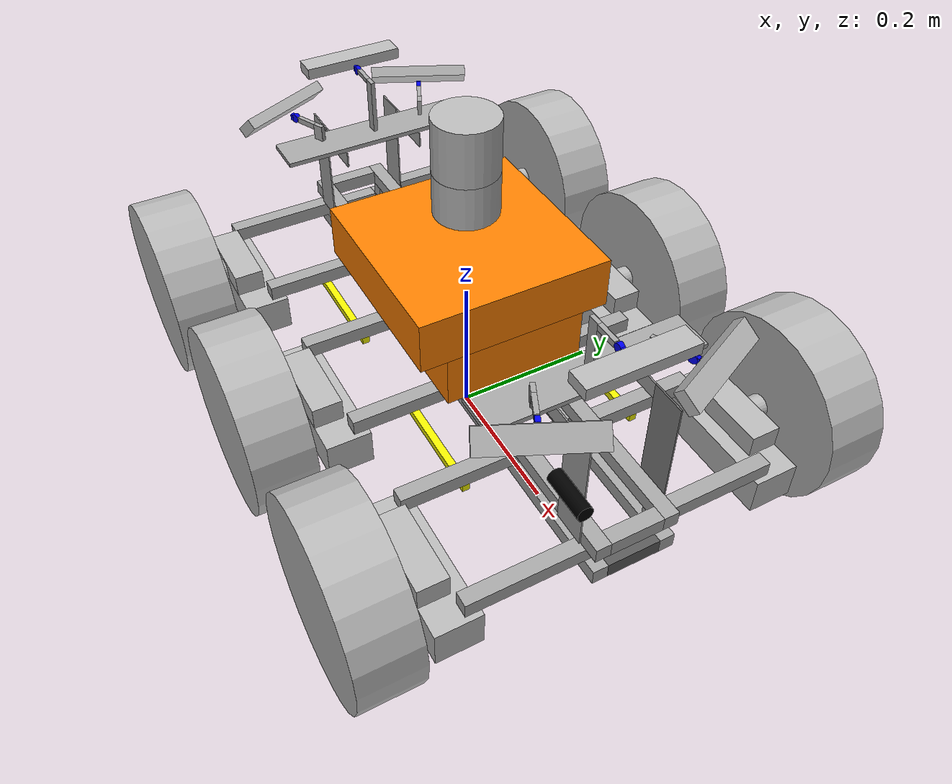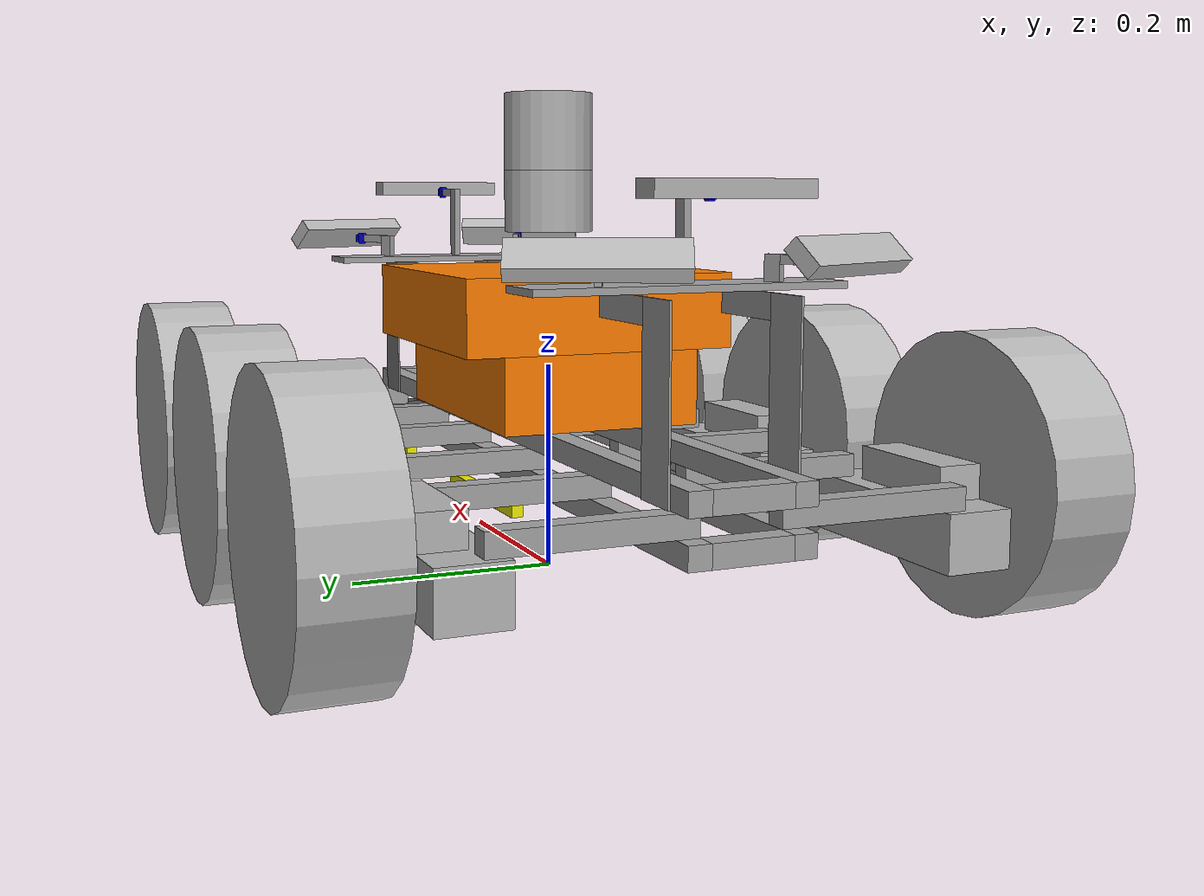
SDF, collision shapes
<?xml version='1.0'?>
 <sdf version='1.5'>
  <model name="siar">

   <static>false</static>

 				<!-- DEFINITION OF LINKS -->

<!-- 1. Definition of Chassis-->

    <link name='chassis_1'>
      <pose>0 0.045 .105 0 0 0</pose>
      <collision name='collision'>
        <geometry>
          <box>
            <size>.796 .02 .02</size>
          </box>
        </geometry>
      </collision>
      <visual name='visual'>
        <geometry>
          <box>
            <size>.796 .02 .02</size>
          </box>
        </geometry>
        <material>
          <ambient>0.7 0.7 0.7 1</ambient>      <!-- Clear gray-->
          <diffuse>0.65 0.65 0.65 1</diffuse>      <!-- Clear gray -->
          <specular>0.6 0.6 0.6 1</specular>    <!-- Clear gray -->
          <emissive>0 0 0 1</emissive>          <!-- Does not emit light -->
        </material>
      </visual>
    </link>

    <link name='chassis_2'>
      <pose>0 -0.045 .105 0 0 0</pose>
      <collision name='collision'>
        <geometry>
          <box>
            <size>.796 .02 .02</size>
          </box>
        </geometry>
      </collision>
      <visual name='visual'>
        <geometry>
          <box>
            <size>.796 .02 .02</size>
          </box>
        </geometry>
        <material>
          <ambient>0.7 0.7 0.7 1</ambient>      <!-- Clear gray-->
          <diffuse>0.65 0.65 0.65 1</diffuse>      <!-- Clear gray -->
          <specular>0.6 0.6 0.6 1</specular>    <!-- Clear gray -->
          <emissive>0 0 0 1</emissive>          <!-- Does not emit light -->
        </material>
      </visual>
    </link>

    <link name='chassis_3'>
      <pose>0.388 .0 .105 0 0 0</pose>
      <collision name='collision'>
        <geometry>
          <box>
            <size>.02 .07 .02</size>
          </box>
        </geometry>
      </collision>
      <visual name='visual'>
        <geometry>
          <box>
            <size>.02 .07 .02</size>
          </box>
        </geometry>
        <material>
          <ambient>0.4 0.4 0.4 1</ambient>      <!-- Gris medio -->
          <diffuse>0.35 0.35 0.35 1</diffuse>      <!-- Gris medio -->
          <specular>0.3 0.3 0.3 1</specular>    <!-- Gris medio -->
          <emissive>0 0 0 1</emissive>          <!-- No emite luz -->
        </material>
      </visual>
    </link>

    <link name='chassis_4'>
      <pose>-0.388 .0 .105 0 0 0</pose>
      <collision name='collision'>
        <geometry>
          <box>
            <size>.02 .07 .02</size>
          </box>
        </geometry>
      </collision>
      <visual name='visual'>
        <geometry>
          <box>
            <size>.02 .07 .02</size>
          </box>
        </geometry>
        <material>
          <ambient>0.7 0.7 0.7 1</ambient>      <!-- Clear gray-->
          <diffuse>0.65 0.65 0.65 1</diffuse>      <!-- Clear gray -->
          <specular>0.6 0.6 0.6 1</specular>    <!-- Clear gray -->
          <emissive>0 0 0 1</emissive>          <!-- Does not emit light -->
        </material>
      </visual>
    </link>

    <joint type="fixed" name="joint_chassis_1_3">
      <pose>.388 0 0 0 0 0</pose>
      <child>chassis_1</child>
      <parent>chassis_3</parent>
    </joint>
    <joint type="fixed" name="joint_chassis_1_4">
      <pose>-.388 0 0 0 0 0</pose>
      <child>chassis_1</child>
      <parent>chassis_4</parent>
    </joint>
    <joint type="fixed" name="joint_chassis_2_3">
      <pose>.388 0 0 0 0 0</pose>
      <child>chassis_2</child>
      <parent>chassis_3</parent>
    </joint>
    <joint type="fixed" name="joint_chassis_2_4">
      <pose>-.388 0 0 0 0 0</pose>
      <child>chassis_2</child>
      <parent>chassis_4</parent>
    </joint>

<!-- 2. Definition of Arms -->

    <link name='arm_right_1_1'>
      <pose>.078 .12 .125 0 0 0</pose>
      <collision name='collision'>
        <geometry>
          <box>
            <size>.02 .17 .02</size>
          </box>
        </geometry>
      </collision>
      <visual name='visual'>
        <geometry>
          <box>
            <size>.02 .17 .02</size>
          </box>
        </geometry>
        <material>
          <ambient>0.7 0.7 0.7 1</ambient>      <!-- Clear gray-->
          <diffuse>0.65 0.65 0.65 1</diffuse>      <!-- Clear gray -->
          <specular>0.6 0.6 0.6 1</specular>    <!-- Clear gray -->
          <emissive>0 0 0 1</emissive>          <!-- Does not emit light -->
        </material>
      </visual>
     </link>

    <link name='arm_right_1_2'>
      <pose>-.078 .12 .125 0 0 0</pose>
      <collision name='collision'>
        <geometry>
          <box>
            <size>.02 .17 .02</size>
          </box>
        </geometry>
      </collision>
      <visual name='visual'>
        <geometry>
          <box>
            <size>.02 .17 .02</size>
          </box>
        </geometry>
        <material>
          <ambient>0.7 0.7 0.7 1</ambient>      <!-- Clear gray-->
          <diffuse>0.65 0.65 0.65 1</diffuse>      <!-- Clear gray -->
          <specular>0.6 0.6 0.6 1</specular>    <!-- Clear gray -->
          <emissive>0 0 0 1</emissive>          <!-- Does not emit light -->
        </material>
      </visual>
     </link>

     <link name='arm_right_2_1'>
      <pose>.214 .12 .125 0 0 0</pose>
      <collision name='collision'>
        <geometry>
          <box>
            <size>.02 .17 .02</size>
          </box>
        </geometry>
      </collision>
      <visual name='visual'>
        <geometry>
          <box>
            <size>.02 .17 .02</size>
          </box>
        </geometry>
        <material>
          <ambient>0.7 0.7 0.7 1</ambient>      <!-- Clear gray-->
          <diffuse>0.65 0.65 0.65 1</diffuse>      <!-- Clear gray -->
          <specular>0.6 0.6 0.6 1</specular>    <!-- Clear gray -->
          <emissive>0 0 0 1</emissive>          <!-- Does not emit light -->
        </material>
      </visual>
     </link>

     <link name='arm_right_2_2'>
      <pose>.37 .12 .125 0 0 0</pose>
      <collision name='collision'>
        <geometry>
          <box>
            <size>.02 .17 .02</size>
          </box>
        </geometry>
      </collision>
      <visual name='visual'>
        <geometry>
          <box>
            <size>.02 .17 .02</size>
          </box>
        </geometry>
        <material>
          <ambient>0.7 0.7 0.7 1</ambient>      <!-- Clear gray-->
          <diffuse>0.65 0.65 0.65 1</diffuse>      <!-- Clear gray -->
          <specular>0.6 0.6 0.6 1</specular>    <!-- Clear gray -->
          <emissive>0 0 0 1</emissive>          <!-- Does not emit light -->
        </material>
      </visual>
     </link>

     <link name='arm_right_3_1'>
      <pose>-.214 .12 .125 0 0 0</pose>
      <collision name='collision'>
        <geometry>
          <box>
            <size>.02 .17 .02</size>
          </box>
        </geometry>
      </collision>
      <visual name='visual'>
        <geometry>
          <box>
            <size>.02 .17 .02</size>
          </box>
        </geometry>
        <material>
          <ambient>0.7 0.7 0.7 1</ambient>      <!-- Clear gray-->
          <diffuse>0.65 0.65 0.65 1</diffuse>      <!-- Clear gray -->
          <specular>0.6 0.6 0.6 1</specular>    <!-- Clear gray -->
          <emissive>0 0 0 1</emissive>          <!-- Does not emit light -->
        </material>
      </visual>
     </link>

     <link name='arm_right_3_2'>
      <pose>-.37 .12 .125 0 0 0</pose>
      <collision name='collision'>
        <geometry>
          <box>
            <size>.02 .17 .02</size>
          </box>
        </geometry>
      </collision>
      <visual name='visual'>
        <geometry>
          <box>
            <size>.02 .17 .02</size>
          </box>
        </geometry>
        <material>
          <ambient>0.7 0.7 0.7 1</ambient>      <!-- Clear gray-->
          <diffuse>0.65 0.65 0.65 1</diffuse>      <!-- Clear gray -->
          <specular>0.6 0.6 0.6 1</specular>    <!-- Clear gray -->
          <emissive>0 0 0 1</emissive>          <!-- Does not emit light -->
        </material>
      </visual>
    </link>

    <link name='arm_left_1_1'>
       <pose>.078 -.12 .125 0 0 0</pose>
       <collision name='collision'>
        <geometry>
          <box>
            <size>.02 .17 .02</size>
          </box>
        </geometry>
      </collision>
      <visual name='visual'>
        <geometry>
          <box>
            <size>.02 .17 .02</size>
          </box>
        </geometry>
        <material>
          <ambient>0.7 0.7 0.7 1</ambient>      <!-- Clear gray-->
          <diffuse>0.65 0.65 0.65 1</diffuse>      <!-- Clear gray -->
          <specular>0.6 0.6 0.6 1</specular>    <!-- Clear gray -->
          <emissive>0 0 0 1</emissive>          <!-- Does not emit light -->
        </material>
      </visual>
    </link>

    <link name='arm_left_1_2'>
      <pose>-.078 -.12 .125 0 0 0</pose>
      <collision name='collision'>
        <geometry>
          <box>
            <size>.02 .17 .02</size>
          </box>
        </geometry>
      </collision>
      <visual name='visual'>
        <geometry>
          <box>
            <size>.02 .17 .02</size>
          </box>
        </geometry>
        <material>
          <ambient>0.7 0.7 0.7 1</ambient>      <!-- Clear gray-->
          <diffuse>0.65 0.65 0.65 1</diffuse>      <!-- Clear gray -->
          <specular>0.6 0.6 0.6 1</specular>    <!-- Clear gray -->
          <emissive>0 0 0 1</emissive>          <!-- Does not emit light -->
        </material>
      </visual>
    </link>

    <link name='arm_left_2_1'>
      <pose>.214 -.12 .125 0 0 0</pose>
      <collision name='collision'>
        <geometry>
          <box>
            <size>.02 .17 .02</size>
          </box>
        </geometry>
      </collision>
      <visual name='visual'>
        <geometry>
          <box>
            <size>.02 .17 .02</size>
          </box>
        </geometry>
        <material>
          <ambient>0.7 0.7 0.7 1</ambient>      <!-- Clear gray-->
          <diffuse>0.65 0.65 0.65 1</diffuse>      <!-- Clear gray -->
          <specular>0.6 0.6 0.6 1</specular>    <!-- Clear gray -->
          <emissive>0 0 0 1</emissive>          <!-- Does not emit light -->
        </material>
      </visual>
    </link>

  <link name='arm_left_2_2'>
      <pose>.37 -.12 .125 0 0 0</pose>
      <collision name='collision'>
        <geometry>
          <box>
            <size>.02 .17 .02</size>
          </box>
        </geometry>
      </collision>
      <visual name='visual'>
        <geometry>
          <box>
            <size>.02 .17 .02</size>
          </box>
        </geometry>
        <material>
          <ambient>0.7 0.7 0.7 1</ambient>      <!-- Clear gray-->
          <diffuse>0.65 0.65 0.65 1</diffuse>      <!-- Clear gray -->
          <specular>0.6 0.6 0.6 1</specular>    <!-- Clear gray -->
          <emissive>0 0 0 1</emissive>          <!-- Does not emit light -->
        </material>
      </visual>
   </link>

  <link name='arm_left_3_1'>
      <pose>-.214 -.12 .125 0 0 0</pose>
      <collision name='collision'>
        <geometry>
          <box>
            <size>.02 .17 .02</size>
          </box>
        </geometry>
      </collision>
      <visual name='visual'>
        <geometry>
          <box>
            <size>.02 .17 .02</size>
          </box>
        </geometry>
        <material>
          <ambient>0.7 0.7 0.7 1</ambient>      <!-- Clear gray-->
          <diffuse>0.65 0.65 0.65 1</diffuse>      <!-- Clear gray -->
          <specular>0.6 0.6 0.6 1</specular>    <!-- Clear gray -->
          <emissive>0 0 0 1</emissive>          <!-- Does not emit light -->
        </material>
      </visual>
   </link>

  <link name='arm_left_3_2'>
      <pose>-.37 -.12 .125 0 0 0</pose>
      <collision name='collision'>
        <geometry>
          <box>
            <size>.02 .17 .02</size>
          </box>
        </geometry>
      </collision>
      <visual name='visual'>
        <geometry>
          <box>
            <size>.02 .17 .02</size>
          </box>
        </geometry>
        <material>
          <ambient>0.7 0.7 0.7 1</ambient>      <!-- Clear gray-->
          <diffuse>0.65 0.65 0.65 1</diffuse>      <!-- Clear gray -->
          <specular>0.6 0.6 0.6 1</specular>    <!-- Clear gray -->
          <emissive>0 0 0 1</emissive>          <!-- Does not emit light -->
        </material>
      </visual>
    </link>

      <joint type="revolute" name="hinge_arm_right_1_1">
      <pose>0 -.075 -0.01 0 0 0</pose>
      <child>arm_right_1_1</child>
      <parent>chassis_1</parent>
      <axis>
        <limit>
          <lower>-1.2</lower>
          <upper>1.2</upper>
        </limit>
        <xyz>0 0 1</xyz>
      </axis>
      </joint>
      <joint type="revolute" name="hinge_arm_right_1_2">
      <pose>0 -.075 -0.01 0 0 0</pose>
      <child>arm_right_1_2</child>
      <parent>chassis_1</parent>
      <axis>
        <limit>
          <lower>-1.2</lower>
          <upper>1.2</upper>
        </limit>
        <xyz>0 0 1</xyz>
      </axis>
      </joint>
      <joint type="revolute" name="hinge_arm_right_2_1">
      <pose>0 -.075 -0.01 0 0 0</pose>
      <child>arm_right_2_1</child>
      <parent>chassis_1</parent>
      <axis>
        <limit>
          <lower>-1.2</lower>
          <upper>1.2</upper>
        </limit>
        <xyz>0 0 1</xyz>
      </axis>
      </joint>

      <joint type="revolute" name="hinge_arm_right_2_2">
      <pose>0 -.075 -0.01 0 0 0</pose>
      <child>arm_right_2_2</child>
      <parent>chassis_1</parent>
      <axis>
        <limit>
          <lower>-1.2</lower>
          <upper>1.2</upper>
        </limit>
        <xyz>0 0 1</xyz>
      </axis>
      </joint>

      <joint type="revolute" name="hinge_arm_right_3_1">
      <pose>0 -.075 -0.01 0 0 0</pose>
      <child>arm_right_3_1</child>
      <parent>chassis_1</parent>
      <axis>
        <limit>
          <lower>-1.2</lower>
          <upper>1.2</upper>
        </limit>
        <xyz>0 0 1</xyz>
      </axis>
      </joint>
      <joint type="revolute" name="hinge_arm_right_3_2">
      <pose>0 -.075 -0.01 0 0 0</pose>
      <child>arm_right_3_2</child>
      <parent>chassis_1</parent>
      <axis>
        <limit>
          <lower>-1.2</lower>
          <upper>1.2</upper>
        </limit>
        <xyz>0 0 1</xyz>
      </axis>
      </joint>
      <joint type="revolute" name="hinge_arm_left_1_1">
      <pose>0 .075 -0.01 0 0 0</pose>
      <child>arm_left_1_1</child>
      <parent>chassis_2</parent>
      <axis>
        <limit>
          <lower>-1.2</lower>
          <upper>1.2</upper>
        </limit>
        <xyz>0 0 1</xyz>
      </axis>
      </joint>
      <joint type="revolute" name="hinge_arm_left_1_2">
      <pose>0 .075 -0.01 0 0 0</pose>
      <child>arm_left_1_2</child>
      <parent>chassis_2</parent>
      <axis>
        <limit>
          <lower>-1.2</lower>
          <upper>1.2</upper>
        </limit>
        <xyz>0 0 1</xyz>
      </axis>
      </joint>
      <joint type="revolute" name="hinge_arm_left_2_1">
      <pose>0 .075 -0.01 0 0 0</pose>
      <child>arm_left_2_1</child>
      <parent>chassis_2</parent>
      <axis>
        <limit>
          <lower>-1.2</lower>
          <upper>1.2</upper>
        </limit>
        <xyz>0 0 1</xyz>
      </axis>
      </joint>
      <joint type="revolute" name="hinge_arm_left_2_2">
      <pose>0 .075 -0.01 0 0 0</pose>
      <child>arm_left_2_2</child>
      <parent>chassis_2</parent>
      <axis>
        <limit>
          <lower>-1.2</lower>
          <upper>1.2</upper>
        </limit>
        <xyz>0 0 1</xyz>
      </axis>
      </joint>
      <joint type="revolute" name="hinge_arm_left_3_1">
      <pose>0 .075 -0.01 0 0 0</pose>
      <child>arm_left_3_1</child>
      <parent>chassis_2</parent>
      <axis>
        <limit>
          <lower>-1.2</lower>
          <upper>1.2</upper>
        </limit>
        <xyz>0 0 1</xyz>
      </axis>
      </joint>
      <joint type="revolute" name="hinge_arm_left_3_2">
      <pose>0 .075 -0.01 0 0 0</pose>
      <child>arm_left_3_2</child>
      <parent>chassis_2</parent>
      <axis>
        <limit>
          <lower>-1.2</lower>
          <upper>1.2</upper>
        </limit>
        <xyz>0 0 1</xyz>
      </axis>
      </joint>

<!-- 3. Definition of Upper Chassis -->

    <link name='chassis_5'>
      <pose>0 0.045 .145 0 0 0</pose>
      <collision name='collision'>
        <geometry>
          <box>
            <size>.796 .02 .02</size>
          </box>
        </geometry>
      </collision>
      <visual name='visual'>
        <geometry>
          <box>
            <size>.796 .02 .02</size>
          </box>
        </geometry>
        <material>
          <ambient>0.7 0.7 0.7 1</ambient>      <!-- Clear gray-->
          <diffuse>0.65 0.65 0.65 1</diffuse>      <!-- Clear gray -->
          <specular>0.6 0.6 0.6 1</specular>    <!-- Clear gray -->
          <emissive>0 0 0 1</emissive>          <!-- Does not emit light -->
        </material>
      </visual>
    </link>

    <link name='chassis_6'>
      <pose>0 -0.045 .145 0 0 0</pose>
      <collision name='collision'>
        <geometry>
          <box>
            <size>.796 .02 .02</size>
          </box>
        </geometry>
      </collision>
      <visual name='visual'>
        <geometry>
          <box>
            <size>.796 .02 .02</size>
          </box>
        </geometry>
        <material>
          <ambient>0.7 0.7 0.7 1</ambient>      <!-- Clear gray-->
          <diffuse>0.65 0.65 0.65 1</diffuse>      <!-- Clear gray -->
          <specular>0.6 0.6 0.6 1</specular>    <!-- Clear gray -->
          <emissive>0 0 0 1</emissive>          <!-- Does not emit light -->
        </material>
      </visual>
    </link>

    <link name='chassis_7'>
      <pose>0.388 .0 .145 0 0 0</pose>
      <collision name='collision'>
        <geometry>
          <box>
            <size>.02 .07 .02</size>
          </box>
        </geometry>
      </collision>
      <visual name='visual'>
        <geometry>
          <box>
            <size>.02 .07 .02</size>
          </box>
        </geometry>
        <material>
          <ambient>0.7 0.7 0.7 1</ambient>      <!-- Clear gray-->
          <diffuse>0.65 0.65 0.65 1</diffuse>      <!-- Clear gray -->
          <specular>0.6 0.6 0.6 1</specular>    <!-- Clear gray -->
          <emissive>0 0 0 1</emissive>          <!-- Does not emit light -->
        </material>
      </visual>
    </link>

    <link name='chassis_8'>
      <pose>-0.388 .0 .145 0 0 0</pose>
      <collision name='collision'>
        <geometry>
          <box>
            <size>.02 .07 .02</size>
          </box>
        </geometry>
      </collision>
      <visual name='visual'>
        <geometry>
          <box>
            <size>.02 .07 .02</size>
          </box>
        </geometry>
        <material>
          <ambient>0.7 0.7 0.7 1</ambient>      <!-- Clear gray-->
          <diffuse>0.65 0.65 0.65 1</diffuse>      <!-- Clear gray -->
          <specular>0.6 0.6 0.6 1</specular>    <!-- Clear gray -->
          <emissive>0 0 0 1</emissive>          <!-- Does not emit light -->
        </material>
      </visual>
    </link>

    <joint type="fixed" name="joint_chassis_5_7">
      <pose>.388 0 0 0 0 0</pose>
      <child>chassis_5</child>
      <parent>chassis_7</parent>
    </joint>
    <joint type="fixed" name="joint_chassis_5_8">
      <pose>-.388 0 0 0 0 0</pose>
      <child>chassis_5</child>
      <parent>chassis_8</parent>
    </joint>
    <joint type="fixed" name="joint_chassis_6_7">
      <pose>.388 0 0 0 0 0</pose>
      <child>chassis_6</child>
      <parent>chassis_7</parent>
    </joint>
    <joint type="fixed" name="joint_chassis_6_8">
      <pose>-.388 0 0 0 0 0</pose>
      <child>chassis_6</child>
      <parent>chassis_8</parent>
    </joint>

      <joint type="revolute" name="upch_arm_right_1_1">
      <pose>0 -.075 0.01 0 0 0</pose>
      <child>arm_right_1_1</child>
      <parent>chassis_5</parent>
      <axis>
        <limit>
          <lower>-1.2</lower>
          <upper>1.2</upper>
        </limit>
        <xyz>0 0 1</xyz>
      </axis>
      </joint>
      <joint type="revolute" name="upch_arm_right_1_2">
      <pose>0 -.075 0.01 0 0 0</pose>
      <child>arm_right_1_2</child>
      <parent>chassis_5</parent>
      <axis>
        <limit>
          <lower>-1.2</lower>
          <upper>1.2</upper>
        </limit>
        <xyz>0 0 1</xyz>
      </axis>
      </joint>
      <joint type="revolute" name="upch_arm_right_2_1">
      <pose>0 -.075 0.01 0 0 0</pose>
      <child>arm_right_2_1</child>
      <parent>chassis_5</parent>
      <axis>
        <limit>
          <lower>-1.2</lower>
          <upper>1.2</upper>
        </limit>
        <xyz>0 0 1</xyz>
      </axis>
      </joint>

      <joint type="revolute" name="upch_arm_right_2_2">
      <pose>0 -.075 0.01 0 0 0</pose>
      <child>arm_right_2_2</child>
      <parent>chassis_5</parent>
      <axis>
        <limit>
          <lower>-1.2</lower>
          <upper>1.2</upper>
        </limit>
        <xyz>0 0 1</xyz>
      </axis>
      </joint>

      <joint type="revolute" name="upch_arm_right_3_1">
      <pose>0 -.075 0.01 0 0 0</pose>
      <child>arm_right_3_1</child>
      <parent>chassis_5</parent>
      <axis>
        <limit>
          <lower>-1.2</lower>
          <upper>1.2</upper>
        </limit>
        <xyz>0 0 1</xyz>
      </axis>
      </joint>
      <joint type="revolute" name="upch_arm_right_3_2">
      <pose>0 -.075 0.01 0 0 0</pose>
      <child>arm_right_3_2</child>
      <parent>chassis_5</parent>
      <axis>
        <limit>
          <lower>-1.2</lower>
          <upper>1.2</upper>
        </limit>
        <xyz>0 0 1</xyz>
      </axis>
      </joint>
      <joint type="revolute" name="upch_arm_left_1_1">
      <pose>0 .075 0.01 0 0 0</pose>
      <child>arm_left_1_1</child>
      <parent>chassis_6</parent>
      <axis>
        <limit>
          <lower>-1.2</lower>
          <upper>1.2</upper>
        </limit>
        <xyz>0 0 1</xyz>
      </axis>
      </joint>
      <joint type="revolute" name="upch_arm_left_1_2">
      <pose>0 .075 0.01 0 0 0</pose>
      <child>arm_left_1_2</child>
      <parent>chassis_6</parent>
      <axis>
        <limit>
          <lower>-1.2</lower>
          <upper>1.2</upper>
        </limit>
        <xyz>0 0 1</xyz>
      </axis>
      </joint>
      <joint type="revolute" name="upch_arm_left_2_1">
      <pose>0 .075 0.01 0 0 0</pose>
      <child>arm_left_2_1</child>
      <parent>chassis_6</parent>
      <axis>
        <limit>
          <lower>-1.2</lower>
          <upper>1.2</upper>
        </limit>
        <xyz>0 0 1</xyz>
      </axis>
      </joint>
      <joint type="revolute" name="upch_arm_left_2_2">
      <pose>0 .075 0.01 0 0 0</pose>
      <child>arm_left_2_2</child>
      <parent>chassis_6</parent>
      <axis>
        <limit>
          <lower>-1.2</lower>
          <upper>1.2</upper>
        </limit>
        <xyz>0 0 1</xyz>
      </axis>
      </joint>
      <joint type="revolute" name="upch_arm_left_3_1">
      <pose>0 .075 0.01 0 0 0</pose>
      <child>arm_left_3_1</child>
      <parent>chassis_6</parent>
      <axis>
        <limit>
          <lower>-1.2</lower>
          <upper>1.2</upper>
        </limit>
        <xyz>0 0 1</xyz>
      </axis>
      </joint>
      <joint type="revolute" name="upch_arm_left_3_2">
      <pose>0 .075 0.01 0 0 0</pose>
      <child>arm_left_3_2</child>
      <parent>chassis_6</parent>
      <axis>
        <limit>
          <lower>-1.2</lower>
          <upper>1.2</upper>
        </limit>
        <xyz>0 0 1</xyz>
      </axis>
      </joint>

<!-- 4. Box of battery and electronic and Handle to Cameras  -->

   <link name="box_battery">
      <collision name='collision_1'>
      <pose>.0 .0 .26 0 0 0</pose>
        <geometry>
          <box>
            <size>.26 .26 .07</size>
          </box>
        </geometry>
      </collision>
      <visual name='visual_1'>
      <pose>.0 .0 .26 0 0 0</pose>
        <geometry>
          <box>
            <size>.26 .26 .07</size>
          </box>
        </geometry>
        <material>
          <ambient>1 0.5 0 1</ambient>      <!-- Orange ambient color -->
          <diffuse>1 0.5 0 1</diffuse>      <!-- Orange diffuse color -->
          <specular>1 0.5 0 1</specular>    <!-- Orange specular color -->
          <emissive>0 0 0 1</emissive>      <!-- No emissive color -->
        </material>
      </visual>
      <collision name='collision_2'>
      <pose>.0 .0 .19 0 0 0</pose>
        <geometry>
          <box>
            <size>.26 .19 .07</size>
          </box>
        </geometry>
      </collision>
      <visual name='visual_2'>
      <pose>.0 .0 .19 0 0 0</pose>
        <geometry>
          <box>
            <size>.26 .19 .07</size>
          </box>
        </geometry>
        <material>
          <ambient>1 0.5 0 1</ambient>      <!-- Orange ambient color -->
          <diffuse>1 0.5 0 1</diffuse>      <!-- Orange diffuse color -->
          <specular>1 0.5 0 1</specular>    <!-- Orange specular color -->
          <emissive>0 0 0 1</emissive>      <!-- No emissive color -->
        </material>
      </visual>
      <visual name='visual_3'>
      <pose>.0 .0 .2975 0 0 0</pose>
        <geometry>
          <box>
            <size>.30 .30 .005</size>
          </box>
        </geometry>
        <material>
          <ambient>0 0 0 1</ambient>      <!-- Black ambient color -->
          <diffuse>0 0 0 1</diffuse>      <!-- Black diffuse color -->
          <specular>0 0 0 1</specular>    <!-- Black specular color -->
          <emissive>0 0 0 1</emissive>    <!-- No emissive color (black) -->
        </material>
      </visual>
      <visual name='visual_4'>
      <pose>.0 .0 .3005 0 0 0</pose>
        <geometry>
          <box>
            <size>.28 .28 .001</size>
          </box>
        </geometry>
        <material>
          <material>
          <ambient>0.35 0.35 .35 1</ambient>      <!-- DarkGray color-->
          <diffuse>0.3 0.3 0.3 1</diffuse>      <!-- DarkGray color -->
          <specular>0.3 0.3 0.3 1</specular>    <!-- DarkGray color -->
          <emissive>0 0 0 1</emissive>          <!-- Does not emit light -->
        </material>
        </material>
      </visual>
      <sensor name="imu_sensor" type="imu">
	<always_on>true</always_on>
	<update_rate>100</update_rate>
	<visualize>true</visualize>
	<topic>imu_siar_topic</topic>
	<pose>0 0 0 0 0 0</pose>
      </sensor>
   </link>

    <joint type="fixed" name="joint_box_1">
      <pose>0 0 0 0 0 0</pose>
      <child>chassis_5</child>
      <parent>box_battery</parent>
    </joint>
    <joint type="fixed" name="joint_box_2">
      <pose>0 0 0 0 0 0</pose>
      <child>chassis_6</child>
      <parent>box_battery</parent>
    </joint>

   <link name="handle_camera_front_1">
      <pose>.3465 .056 .213 0 0 0</pose>
      <collision name='collision_1'>
        <geometry>
          <box>
            <size>.045 .002 .156</size>
          </box>
        </geometry>
      </collision>
      <visual name='visual_1'>
        <geometry>
          <box>
            <size>.045 .002 .156 </size>
          </box>
        </geometry>
        <material>
          <ambient>0.5 0.5 0.5 1</ambient>      <!-- Gris medio -->
          <diffuse>0.5 0.5 0.5 1</diffuse>      <!-- Gris medio -->
          <specular>0.5 0.5 0.5 1</specular>    <!-- Gris medio -->
          <emissive>0 0 0 1</emissive>          <!-- No emite luz -->
        </material>
      </visual>
   </link>

   <link name="handle_camera_front_1_1">
      <pose>.285 .056 .28 0 0 0</pose>
      <collision name='collision_1'>
        <geometry>
          <box>
            <size>.078 .002 .022</size>
          </box>
        </geometry>
      </collision>
      <visual name='visual_1'>
        <geometry>
          <box>
            <size>.078 .002 .022 </size>
          </box>
        </geometry>
        <material>
          <ambient>0.7 0.7 0.7 1</ambient>      <!-- Clear gray-->
          <diffuse>0.65 0.65 0.65 1</diffuse>      <!-- Clear gray -->
          <specular>0.6 0.6 0.6 1</specular>    <!-- Clear gray -->
          <emissive>0 0 0 1</emissive>          <!-- Does not emit light -->
        </material>
      </visual>
   </link>

   <link name="handle_camera_front_2">
      <pose>.3465 -.056 .213 0 0 0</pose>
      <collision name='collision_1'>
        <geometry>
          <box>
            <size>.045 .002 .156</size>
          </box>
        </geometry>
      </collision>
      <visual name='visual_1'>
        <geometry>
          <box>
            <size>.045 .002 .156 </size>
          </box>
        </geometry>
        <material>
          <ambient>0.7 0.7 0.7 1</ambient>      <!-- Clear gray-->
          <diffuse>0.65 0.65 0.65 1</diffuse>      <!-- Clear gray -->
          <specular>0.6 0.6 0.6 1</specular>    <!-- Clear gray -->
          <emissive>0 0 0 1</emissive>          <!-- Does not emit light -->
        </material>
      </visual>
   </link>

   <link name="handle_camera_front_2_1">
      <pose>.285 -.056 .28 0 0 0</pose>
      <collision name='collision_1'>
        <geometry>
          <box>
            <size>.078 .002 .022</size>
          </box>
        </geometry>
      </collision>
      <visual name='visual_1'>
        <geometry>
          <box>
            <size>.078 .002 .022 </size>
          </box>
        </geometry>
        <material>
          <ambient>0.7 0.7 0.7 1</ambient>      <!-- Clear gray-->
          <diffuse>0.65 0.65 0.65 1</diffuse>      <!-- Clear gray -->
          <specular>0.6 0.6 0.6 1</specular>    <!-- Clear gray -->
          <emissive>0 0 0 1</emissive>          <!-- Does not emit light -->
        </material>
      </visual>
   </link>

   <joint type="fixed" name="joint_handle_camera_front_1">
     <pose>0 0 -0.078 0 0 0</pose>
     <child>handle_camera_front_1</child>
     <parent>chassis_6</parent>
   </joint>

   <joint type="fixed" name="joint_handle_camera_front_1_1">
     <pose>0.039 0 0 0 0 0</pose>
     <parent>handle_camera_front_1</parent>
     <child>handle_camera_front_1_1</child>
   </joint>

   <joint type="fixed" name="joint_handle_camera_front_2">
     <pose>0 0 -0.078 0 0 0</pose>
     <child>handle_camera_front_2</child>
     <parent>chassis_6</parent>
   </joint>

   <joint type="fixed" name="joint_handle_camera_front_2_1">
     <pose>0.039 0 0 0 0 0</pose>
     <parent>handle_camera_front_2</parent>
     <child>handle_camera_front_2_1</child>
   </joint>

   <link name="handle_camera_back_1">
      <pose>-.3465 .056 .213 0 0 0</pose>
      <collision name='collision_1'>
        <geometry>
          <box>
            <size>.045 .002 .156</size>
          </box>
        </geometry>
      </collision>
      <visual name='visual_1'>
        <geometry>
          <box>
            <size>.045 .002 .156 </size>
          </box>
        </geometry>
        <material>
          <ambient>0.7 0.7 0.7 1</ambient>      <!-- Clear gray-->
          <diffuse>0.65 0.65 0.65 1</diffuse>      <!-- Clear gray -->
          <specular>0.6 0.6 0.6 1</specular>    <!-- Clear gray -->
          <emissive>0 0 0 1</emissive>          <!-- Does not emit light -->
        </material>
      </visual>
    </link>

    <link name="handle_camera_back_1_1">
      <pose>-.285 .056 .28 0 0 0</pose>
      <collision name='collision_1'>
        <geometry>
          <box>
            <size>.078 .002 .022</size>
          </box>
        </geometry>
      </collision>
      <visual name='visual_1'>
        <geometry>
          <box>
            <size>.078 .002 .022 </size>
          </box>
        </geometry>
        <material>
          <ambient>0.7 0.7 0.7 1</ambient>      <!-- Clear gray-->
          <diffuse>0.65 0.65 0.65 1</diffuse>      <!-- Clear gray -->
          <specular>0.6 0.6 0.6 1</specular>    <!-- Clear gray -->
          <emissive>0 0 0 1</emissive>          <!-- Does not emit light -->
        </material>
      </visual>
   </link>

   <link name="handle_camera_back_2">
      <pose>-.3465 -.056 .213 0 0 0</pose>
      <collision name='collision_1'>
        <geometry>
          <box>
            <size>.045 .002 .156</size>
          </box>
        </geometry>
      </collision>
      <visual name='visual_1'>
        <geometry>
          <box>
            <size>.045 .002 .156 </size>
          </box>
        </geometry>
        <material>
          <ambient>0.7 0.7 0.7 1</ambient>      <!-- Clear gray-->
          <diffuse>0.65 0.65 0.65 1</diffuse>      <!-- Clear gray -->
          <specular>0.6 0.6 0.6 1</specular>    <!-- Clear gray -->
          <emissive>0 0 0 1</emissive>          <!-- Does not emit light -->
        </material>
      </visual>
   </link>

   <link name="handle_camera_back_2_1">
      <pose>-.285 -.056 .28 0 0 0</pose>
      <collision name='collision_2'>
        <geometry>
          <box>
            <size>.078 .002 .022</size>
          </box>
        </geometry>
      </collision>
      <visual name='visual_2'>
        <geometry>
          <box>
            <size>.078 .002 .022 </size>
          </box>
        </geometry>
        <material>
          <ambient>0.7 0.7 0.7 1</ambient>      <!-- Clear gray-->
          <diffuse>0.65 0.65 0.65 1</diffuse>      <!-- Clear gray -->
          <specular>0.6 0.6 0.6 1</specular>    <!-- Clear gray -->
          <emissive>0 0 0 1</emissive>          <!-- Does not emit light -->
        </material>
      </visual>
   </link>

   <joint type="fixed" name="joint_handle_camera_back_1">
     <pose>0 0 -0.078 0 0 0</pose>
     <child>handle_camera_back_1</child>
     <parent>chassis_5</parent>
   </joint>

   <joint type="fixed" name="joint_handle_camera_back_1_1">
     <pose>-0.039 0 0 0 0 0</pose>
     <parent>handle_camera_back_1</parent>
     <child>handle_camera_back_1_1</child>
   </joint>

   <joint type="fixed" name="joint_handle_camera_back_2">
     <pose>0 0 -0.078 0 0 0</pose>
     <child>handle_camera_back_2</child>
     <parent>chassis_5</parent>
   </joint>

   <joint type="fixed" name="joint_handle_camera_back_2_1">
     <pose>-0.039 0 0 0 0 0</pose>
     <parent>handle_camera_back_2</parent>
     <child>handle_camera_back_2_1</child>
   </joint>

   <link name="handle_camera_front_3">
      <pose>.2775 .0 .294 0 0 0</pose>
      <collision name='collision'>
        <geometry>
          <box>
            <size>.055 .278 .006 </size>
          </box>
        </geometry>
      </collision>
      <visual name='visual'>
        <geometry>
          <box>
            <size>.055 .278 .006 </size>
          </box>
        </geometry>
        <material>
          <ambient>0.7 0.7 0.7 1</ambient>      <!-- Clear gray-->
          <diffuse>0.65 0.65 0.65 1</diffuse>      <!-- Clear gray -->
          <specular>0.6 0.6 0.6 1</specular>    <!-- Clear gray -->
          <emissive>0 0 0 1</emissive>          <!-- Does not emit light -->
        </material>
      </visual>
   </link>

   <link name="handle_camera_back_3">
      <pose>-.2775 .0 .294 0 0 0</pose>
      <collision name='collision'>
        <geometry>
          <box>
            <size>.055 .278 .006 </size>
          </box>
        </geometry>
      </collision>
      <visual name='visual'>
        <geometry>
          <box>
            <size>.055 .278 .006 </size>
          </box>
        </geometry>
        <material>
          <ambient>0.7 0.7 0.7 1</ambient>      <!-- Clear gray-->
          <diffuse>0.65 0.65 0.65 1</diffuse>      <!-- Clear gray -->
          <specular>0.6 0.6 0.6 1</specular>    <!-- Clear gray -->
          <emissive>0 0 0 1</emissive>          <!-- Does not emit light -->
        </material>
      </visual>
   </link>

    <joint type="fixed" name="joint_handle_camera_front_3_1">
      <pose>0 0.056 -0.001 0 0 0</pose>
      <child>handle_camera_front_3</child>
      <parent>handle_camera_front_1_1</parent>
    </joint>

    <joint type="fixed" name="joint_handle_camera_front_3_2">
      <pose>0 -0.056 -0.001 0 0 0</pose>
      <child>handle_camera_front_3</child>
      <parent>handle_camera_front_2_1</parent>
    </joint>

    <joint type="fixed" name="joint_handle_camera_back_3_1">
      <pose>0 0.056 -0.001 0 0 0</pose>
      <child>handle_camera_back_3</child>
      <parent>handle_camera_back_1_1</parent>
    </joint>

    <joint type="fixed" name="joint_handle_camera_back_3_2">
      <pose>0 -0.056 -0.001 0 0 0</pose>
      <child>handle_camera_back_3</child>
      <parent>handle_camera_back_2_1</parent>
    </joint>

   <link name="handle_camera_front_4_1">
      <pose>.28 .0 .3345 0 0 0</pose>
      <collision name="collision_1">
        <geometry>
          <box>
            <size>.015 .006 .075 </size>
          </box>
        </geometry>
      </collision>
      <visual name="visual_1">
        <geometry>
          <box>
            <size>.015 .006 .075 </size>
          </box>
        </geometry>
        <material>
          <ambient>0.7 0.7 0.7 1</ambient>      <!-- Clear gray-->
          <diffuse>0.65 0.65 0.65 1</diffuse>      <!-- Clear gray -->
          <specular>0.6 0.6 0.6 1</specular>    <!-- Clear gray -->
          <emissive>0 0 0 1</emissive>          <!-- Does not emit light -->
        </material>
      </visual>
   </link>

   <link name="handle_camera_front_4_1_1">
      <pose>.3025 .0 .368 0 0 0</pose>
      <collision name="collision_2">
        <geometry>
          <box>
            <size>.03 .006 .008 </size>
          </box>
        </geometry>
      </collision>
      <visual name="visual_2">
        <geometry>
          <box>
            <size>.03 .006 .008 </size>
          </box>
        </geometry>
        <material>
          <ambient>0.7 0.7 0.7 1</ambient>      <!-- Clear gray-->
          <diffuse>0.65 0.65 0.65 1</diffuse>      <!-- Clear gray -->
          <specular>0.6 0.6 0.6 1</specular>    <!-- Clear gray -->
          <emissive>0 0 0 1</emissive>          <!-- Does not emit light -->
        </material>
      </visual>
   </link>

   <joint type="fixed" name="joint_handle_camera_front_4_1">
     <pose>0 0 -.0375 0 0 0</pose>
     <child>handle_camera_front_4_1</child>
     <parent>handle_camera_front_3</parent>
   </joint>
   <joint type="fixed" name="joint_handle_camera_front_4_1_1">
     <pose>-0.015 0 0 0 0 0</pose>
     <child>handle_camera_front_4_1_1</child>
     <parent>handle_camera_front_4_1</parent>
   </joint>

   <link name="handle_camera_front_4_2">
      <pose>.29 .078 .3082 0 0 0.436332</pose>
      <collision name="collision_1">
        <geometry>
          <box>
            <size>.015 .006 .0224 </size>
          </box>
        </geometry>
      </collision>
      <visual name="visual_1">
        <geometry>
          <box>
            <size>.015 .006 .0224 </size>
          </box>
        </geometry>
        <material>
          <ambient>0.7 0.7 0.7 1</ambient>      <!-- Clear gray-->
          <diffuse>0.65 0.65 0.65 1</diffuse>      <!-- Clear gray -->
          <specular>0.6 0.6 0.6 1</specular>    <!-- Clear gray -->
          <emissive>0 0 0 1</emissive>          <!-- Does not emit light -->
        </material>
      </visual>
    </link>

    <link name="handle_camera_front_4_2_1">
      <pose>.3103 .0875 .3154 0 0 0.436332</pose>
      <collision name="collision_2">
        <geometry>
          <box>
            <size>.03 .006 .008 </size>
          </box>
        </geometry>
      </collision>
      <visual name="visual_2">
        <geometry>
          <box>
            <size>.03 .006 .008 </size>
          </box>
        </geometry>
        <material>
          <ambient>0.7 0.7 0.7 1</ambient>      <!-- Clear gray-->
          <diffuse>0.65 0.65 0.65 1</diffuse>      <!-- Clear gray -->
          <specular>0.6 0.6 0.6 1</specular>    <!-- Clear gray -->
          <emissive>0 0 0 1</emissive>          <!-- Does not emit light -->
        </material>
      </visual>
   </link>

   <joint type="fixed" name="joint_handle_camera_front_4_2">
     <pose>0 0 -.0112 0 0 0</pose>
     <child>handle_camera_front_4_2</child>
     <parent>handle_camera_front_3</parent>
   </joint>
   <joint type="fixed" name="joint_handle_camera_front_4_2_1">
     <pose>-0.015 0 0 0 0 0</pose>
     <child>handle_camera_front_4_2_1</child>
     <parent>handle_camera_front_4_2</parent>
   </joint>

   <link name="handle_camera_front_4_3">
      <pose>.29 -.078 .3082 0 0 -0.436332</pose>
      <collision name="collision_1">
        <geometry>
          <box>
            <size>.015 .006 .0224 </size>
          </box>
        </geometry>
      </collision>
      <visual name="visual_1">
        <geometry>
          <box>
            <size>.015 .006 .0224 </size>
          </box>
        </geometry>
        <material>
          <ambient>0.7 0.7 0.7 1</ambient>      <!-- Clear gray-->
          <diffuse>0.65 0.65 0.65 1</diffuse>      <!-- Clear gray -->
          <specular>0.6 0.6 0.6 1</specular>    <!-- Clear gray -->
          <emissive>0 0 0 1</emissive>          <!-- Does not emit light -->
        </material>
      </visual>
   </link>

   <link name="handle_camera_front_4_3_1">
      <pose>.3103 -.0875 .3154 0 0 -0.436332</pose>
      <collision name="collision_2">
        <geometry>
          <box>
            <size>.03 .006 .008 </size>
          </box>
        </geometry>
      </collision>
      <visual name="visual_2">
        <geometry>
          <box>
            <size>.03 .006 .008 </size>
          </box>
        </geometry>
        <material>
          <ambient>0.7 0.7 0.7 1</ambient>      <!-- Clear gray-->
          <diffuse>0.65 0.65 0.65 1</diffuse>      <!-- Clear gray -->
          <specular>0.6 0.6 0.6 1</specular>    <!-- Clear gray -->
          <emissive>0 0 0 1</emissive>          <!-- Does not emit light -->
        </material>
      </visual>
   </link>

   <joint type="fixed" name="joint_handle_camera_front_4_3">
     <pose>0 0 -.0112 0 0 0</pose>
     <child>handle_camera_front_4_3</child>
     <parent>handle_camera_front_3</parent>
   </joint>
   <joint type="fixed" name="joint_handle_camera_front_4_3_1">
     <pose>-0.015 0 0 0 0 0</pose>
     <child>handle_camera_front_4_3_1</child>
     <parent>handle_camera_front_4_3</parent>
   </joint>

   <link name="handle_camera_back_4_1">
      <pose>-.28 .0 .3345 0 0 0</pose>
      <collision name='collision'>
        <geometry>
          <box>
            <size>.015 .006 .075 </size>
          </box>
        </geometry>
      </collision>
      <visual name='visual'>
        <geometry>
          <box>
            <size>.015 .006 .075 </size>
          </box>
        </geometry>
        <material>
          <ambient>0.7 0.7 0.7 1</ambient>      <!-- Clear gray-->
          <diffuse>0.65 0.65 0.65 1</diffuse>      <!-- Clear gray -->
          <specular>0.6 0.6 0.6 1</specular>    <!-- Clear gray -->
          <emissive>0 0 0 1</emissive>          <!-- Does not emit light -->
        </material>
      </visual>
   </link>

   <link name="handle_camera_back_4_1_1">
      <pose>-.3025 .0 .369 0 0 0</pose>
      <collision name="collision_2">
        <geometry>
          <box>
            <size>.03 .006 .006 </size>
          </box>
        </geometry>
      </collision>
      <visual name="visual_2">
        <geometry>
          <box>
            <size>.03 .006 .006 </size>
          </box>
        </geometry>
        <material>
          <ambient>0.7 0.7 0.7 1</ambient>      <!-- Clear gray-->
          <diffuse>0.65 0.65 0.65 1</diffuse>      <!-- Clear gray -->
          <specular>0.6 0.6 0.6 1</specular>    <!-- Clear gray -->
          <emissive>0 0 0 1</emissive>          <!-- Does not emit light -->
        </material>
      </visual>
   </link>

   <joint type="fixed" name="joint_handle_camera_back_4_1">
     <pose>0 0 -.0375 0 0 0</pose>
     <child>handle_camera_back_4_1</child>
     <parent>handle_camera_back_3</parent>
   </joint>
   <joint type="fixed" name="joint_handle_camera_back_4_1_1">
     <pose>0.015 0 0 0 0 0</pose>
     <child>handle_camera_back_4_1_1</child>
     <parent>handle_camera_back_4_1</parent>
   </joint>

   <link name="handle_camera_back_4_2">
      <pose>-.29 .078 .3082 0 0 -0.436332</pose>
      <collision name="collision_1">
        <geometry>
          <box>
            <size>.015 .006 .0224 </size>
          </box>
        </geometry>
      </collision>
      <visual name="visual_1">
        <geometry>
          <box>
            <size>.015 .006 .0224 </size>
          </box>
        </geometry>
        <material>
          <ambient>0.7 0.7 0.7 1</ambient>      <!-- Clear gray-->
          <diffuse>0.65 0.65 0.65 1</diffuse>      <!-- Clear gray -->
          <specular>0.6 0.6 0.6 1</specular>    <!-- Clear gray -->
          <emissive>0 0 0 1</emissive>          <!-- Does not emit light -->
        </material>
      </visual>
   </link>

   <link name="handle_camera_back_4_2_1">
      <pose>-.3103 .0875 .3154 0 0 -0.436332</pose>
      <collision name="collision_2">
        <geometry>
          <box>
            <size>.03 .006 .008 </size>
          </box>
        </geometry>
      </collision>
      <visual name="visual_2">
        <geometry>
          <box>
            <size>.03 .006 .008 </size>
          </box>
        </geometry>
        <material>
          <ambient>0.7 0.7 0.7 1</ambient>      <!-- Clear gray-->
          <diffuse>0.65 0.65 0.65 1</diffuse>      <!-- Clear gray -->
          <specular>0.6 0.6 0.6 1</specular>    <!-- Clear gray -->
          <emissive>0 0 0 1</emissive>          <!-- Does not emit light -->
        </material>
      </visual>
   </link>

   <joint type="fixed" name="joint_handle_camera_back_4_2">
     <pose>0 0 -.0112 0 0 0</pose>
     <child>handle_camera_back_4_2</child>
     <parent>handle_camera_back_3</parent>
   </joint>
   <joint type="fixed" name="joint_handle_camera_back_4_2_1">
     <pose>-0.015 0 0 0 0 0</pose>
     <child>handle_camera_back_4_2_1</child>
     <parent>handle_camera_back_4_2</parent>
   </joint>

   <link name="handle_camera_back_4_3">
      <pose>-.29 -.078 .3082 0 0 0.436332</pose>
      <collision name="collision_1">
        <geometry>
          <box>
            <size>.015 .006 .0224 </size>
          </box>
        </geometry>
      </collision>
      <visual name="visual_1">
        <geometry>
          <box>
            <size>.015 .006 .0224 </size>
          </box>
        </geometry>
        <material>
          <ambient>0.7 0.7 0.7 1</ambient>      <!-- Clear gray-->
          <diffuse>0.65 0.65 0.65 1</diffuse>      <!-- Clear gray -->
          <specular>0.6 0.6 0.6 1</specular>    <!-- Clear gray -->
          <emissive>0 0 0 1</emissive>          <!-- Does not emit light -->
        </material>
      </visual>
   </link>

   <link name="handle_camera_back_4_3_1">
      <pose>-.3103 -.0875 .3154 0 0 0.436332</pose>
      <collision name="collision_2">
        <geometry>
          <box>
            <size>.03 .006 .008 </size>
          </box>
        </geometry>
      </collision>
      <visual name="visual_2">
        <geometry>
          <box>
            <size>.03 .006 .008 </size>
          </box>
        </geometry>
        <material>
          <ambient>0.7 0.7 0.7 1</ambient>      <!-- Clear gray-->
          <diffuse>0.65 0.65 0.65 1</diffuse>      <!-- Clear gray -->
          <specular>0.6 0.6 0.6 1</specular>    <!-- Clear gray -->
          <emissive>0 0 0 1</emissive>          <!-- Does not emit light -->
        </material>
      </visual>
   </link>

   <joint type="fixed" name="joint_handle_camera_back_4_3">
     <pose>0 0 -.0112 0 0 0</pose>
     <child>handle_camera_back_4_3</child>
     <parent>handle_camera_back_3</parent>
   </joint>
   <joint type="fixed" name="joint_handle_camera_back_4_3_1">
     <pose>-0.015 0 0 0 0 0</pose>
     <child>handle_camera_back_4_3_1</child>
     <parent>handle_camera_back_4_3</parent>
   </joint>

      <link name="pivot_camera_front_1">
        <collision name="collision_1">
         <pose>0.3235 0 .368 0 1.5707 1.5707</pose>
          <geometry>
            <cylinder>
              <radius>.006</radius>
              <length>.006</length>
            </cylinder>
          </geometry>
        </collision>
        <visual name="visual_1">
         <pose>0.3235 0 .368 0 1.5707 1.5707</pose>
          <geometry>
            <cylinder>
              <radius>.006</radius>
              <length>.006</length>
            </cylinder>
          </geometry>
          <material>
            <ambient>0 0 1 1</ambient>      <!-- Blue color-->
            <diffuse>0 0 0.95 1</diffuse>      <!-- Blue color -->
            <specular>0 0 0.9 1</specular>    <!-- Blue color -->
            <emissive>0 0 0 1</emissive>          <!-- Does not emit light -->
          </material>
          </visual>
        <collision name="collision_2">
        <pose>0.3295 0 .368 0 0 0</pose>
          <geometry>
            <box>
              <size>.004 .006 .008 </size>
            </box>
          </geometry>
        </collision>
        <visual name="visual_2">
        <pose>0.3295 0 .368 0 0 0</pose>
          <geometry>
            <box>
              <size>.004 .006 .008 </size>
            </box>
          </geometry>
          <material>
            <ambient>0 0 1 1</ambient>      <!-- Blue color-->
            <diffuse>0 0 0.95 1</diffuse>      <!-- Blue color -->
            <specular>0 0 0.9 1</specular>    <!-- Blue color -->
            <emissive>0 0 0 1</emissive>          <!-- Does not emit light -->
          </material>
        </visual>
      </link>
      <link name="pivot_camera_front_2">
        <collision name="collision_1">
         <pose>0.3295 0.0965 .3154 0 1.5707 -1.13446</pose>
          <geometry>
            <cylinder>
              <radius>.006</radius>
              <length>.006</length>
            </cylinder>
          </geometry>
        </collision>
        <visual name="visual_1">
         <pose>0.3295 0.0965 .3154 0 1.5707 -1.13446</pose>
          <geometry>
            <cylinder>
              <radius>.006</radius>
              <length>.006</length>
            </cylinder>
          </geometry>
          <material>
          <ambient>0 0 1 1</ambient>      <!-- Blue color-->
          <diffuse>0 0 0.95 1</diffuse>      <!-- Blue color -->
          <specular>0 0 0.9 1</specular>    <!-- Blue color -->
          <emissive>0 0 0 1</emissive>          <!-- Does not emit light -->
        </material>
          </visual>
        <collision name="collision_2">
        <pose>0.3345 0.099 .3154 0 0 0.436332</pose>
          <geometry>
            <box>
              <size>.004 .006 .008 </size>
            </box>
          </geometry>
        </collision>
        <visual name="visual_2">
        <pose>0.3345 0.099 .3154 0 0 0.436332</pose>
          <geometry>
            <box>
              <size>.004 .006 .008 </size>
            </box>
          </geometry>
          <material>
          <ambient>0 0 1 1</ambient>      <!-- Blue color-->
          <diffuse>0 0 0.95 1</diffuse>      <!-- Blue color -->
          <specular>0 0 0.9 1</specular>    <!-- Blue color -->
          <emissive>0 0 0 1</emissive>          <!-- Does not emit light -->
        </material>
        </visual>
      </link>
      <link name="pivot_camera_front_3">
        <collision name="collision_1">
         <pose>0.3295 -0.0965 .3154 0 1.5707 1.13446</pose>
          <geometry>
            <cylinder>
              <radius>.006</radius>
              <length>.006</length>
            </cylinder>
          </geometry>
        </collision>
        <visual name="visual_1">
         <pose>0.3295 -0.0965 .3154 0 1.5707 1.13446</pose>
          <geometry>
            <cylinder>
              <radius>.006</radius>
              <length>.006</length>
            </cylinder>
          </geometry>
          <material>
          <ambient>0 0 1 1</ambient>      <!-- Blue color-->
          <diffuse>0 0 0.95 1</diffuse>      <!-- Blue color -->
          <specular>0 0 0.9 1</specular>    <!-- Blue color -->
          <emissive>0 0 0 1</emissive>          <!-- Does not emit light -->
        </material>
          </visual>
        <collision name="collision_2">
        <pose>0.3345 -0.099 .3154 0 0 -0.436332</pose>
          <geometry>
            <box>
              <size>.004 .006 .008 </size>
            </box>
          </geometry>
        </collision>
        <visual name="visual_2">
        <pose>0.3345 -0.099 .3154 0 0 -0.436332</pose>
          <geometry>
            <box>
              <size>.004 .006 .008 </size>
            </box>
          </geometry>
          <material>
          <ambient>0 0 1 1</ambient>      <!-- Blue color-->
          <diffuse>0 0 0.95 1</diffuse>      <!-- Blue color -->
          <specular>0 0 0.9 1</specular>    <!-- Blue color -->
          <emissive>0 0 0 1</emissive>          <!-- Does not emit light -->
        </material>
        </visual>
      </link>

      <link name="pivot_camera_back_1">
        <collision name="collision_1">
         <pose>-0.3235 0 .368 0 1.5707 1.5707</pose>
          <geometry>
            <cylinder>
              <radius>.006</radius>
              <length>.006</length>
            </cylinder>
          </geometry>
        </collision>
        <visual name="visual_1">
         <pose>-0.3235 0 .368 0 1.5707 1.5707</pose>
          <geometry>
            <cylinder>
              <radius>.006</radius>
              <length>.006</length>
            </cylinder>
          </geometry>
          <material>
          <ambient>0 0 1 1</ambient>      <!-- Blue color-->
          <diffuse>0 0 0.95 1</diffuse>      <!-- Blue color -->
          <specular>0 0 0.9 1</specular>    <!-- Blue color -->
          <emissive>0 0 0 1</emissive>          <!-- Does not emit light -->
        </material>
          </visual>
        <collision name="collision_2">
        <pose>-0.3295 0 .368 0 0 0</pose>
          <geometry>
            <box>
              <size>.004 .006 .008 </size>
            </box>
          </geometry>
        </collision>
        <visual name="visual_2">
        <pose>-0.3295 0 .368 0 0 0</pose>
          <geometry>
            <box>
              <size>.004 .006 .008 </size>
            </box>
          </geometry>
          <material>
          <ambient>0 0 1 1</ambient>      <!-- Blue color-->
          <diffuse>0 0 0.95 1</diffuse>      <!-- Blue color -->
          <specular>0 0 0.9 1</specular>    <!-- Blue color -->
          <emissive>0 0 0 1</emissive>          <!-- Does not emit light -->
        </material>
        </visual>
      </link>
      <link name="pivot_camera_back_2">
        <collision name="collision_1">
         <pose>-0.3295 0.0965 .3154 0 1.5707 1.13446</pose>
          <geometry>
            <cylinder>
              <radius>.006</radius>
              <length>.006</length>
            </cylinder>
          </geometry>
        </collision>
        <visual name="visual_1">
         <pose>-0.3295 0.0965 .3154 0 1.5707 1.13446</pose>
          <geometry>
            <cylinder>
              <radius>.006</radius>
              <length>.006</length>
            </cylinder>
          </geometry>
          <material>
          <ambient>0 0 1 1</ambient>      <!-- Blue color-->
          <diffuse>0 0 0.95 1</diffuse>      <!-- Blue color -->
          <specular>0 0 0.9 1</specular>    <!-- Blue color -->
          <emissive>0 0 0 1</emissive>          <!-- Does not emit light -->
        </material>
          </visual>
        <collision name="collision_2">
        <pose>-0.3345 0.099 .3154 0 0 -0.436332</pose>
          <geometry>
            <box>
              <size>.004 .006 .008 </size>
            </box>
          </geometry>
        </collision>
        <visual name="visual_2">
        <pose>-0.3345 0.099 .3154 0 0 -0.436332</pose>
          <geometry>
            <box>
              <size>.004 .006 .008 </size>
            </box>
          </geometry>
          <material>
          <ambient>0 0 1 1</ambient>      <!-- Blue color-->
          <diffuse>0 0 0.95 1</diffuse>      <!-- Blue color -->
          <specular>0 0 0.9 1</specular>    <!-- Blue color -->
          <emissive>0 0 0 1</emissive>          <!-- Does not emit light -->
        </material>
        </visual>
      </link>
      <link name="pivot_camera_back_3">
        <collision name="collision_1">
         <pose>-0.3295 -0.0965 .3154 0 1.5707 -1.13446</pose>
          <geometry>
            <cylinder>
              <radius>.006</radius>
              <length>.006</length>
            </cylinder>
          </geometry>
        </collision>
        <visual name="visual_1">
         <pose>-0.3295 -0.0965 .3154 0 1.5707 -1.13446</pose>
          <geometry>
            <cylinder>
              <radius>.006</radius>
              <length>.006</length>
            </cylinder>
          </geometry>
          <material>
          <ambient>0 0 1 1</ambient>      <!-- Blue color-->
          <diffuse>0 0 0.95 1</diffuse>      <!-- Blue color -->
          <specular>0 0 0.9 1</specular>    <!-- Blue color -->
          <emissive>0 0 0 1</emissive>          <!-- Does not emit light -->
        </material>
          </visual>
        <collision name="collision_2">
        <pose>-0.3345 -0.099 .3154 0 0 0.436332</pose>
          <geometry>
            <box>
              <size>.004 .006 .008 </size>
            </box>
          </geometry>
        </collision>
        <visual name="visual_2">
        <pose>-0.3345 -0.099 .3154 0 0 0.436332</pose>
          <geometry>
            <box>
              <size>.004 .006 .008 </size>
            </box>
          </geometry>
          <material>
          <ambient>0 0 1 1</ambient>      <!-- Blue color-->
          <diffuse>0 0 0.95 1</diffuse>      <!-- Blue color -->
          <specular>0 0 0.9 1</specular>    <!-- Blue color -->
          <emissive>0 0 0 1</emissive>          <!-- Does not emit light -->
        </material>
        </visual>
      </link>

    <joint type="fixed" name="move_camera_front_1"> <!-- To give movement to the cameras, use type revolute, and the example below -->
      <pose>0.3235 0 .368 0 0 0</pose>
      <child>pivot_camera_front_1</child>
      <parent>handle_camera_front_4_1</parent>
    </joint>
   <joint type="fixed" name="move_camera_front_2">
      <pose>0.3295 0.0965 .3154 0 0 0.436332</pose>
      <child>pivot_camera_front_2</child>
      <parent>handle_camera_front_4_2</parent>
    </joint>
   <joint type="fixed" name="move_camera_front_3">
      <pose>0.3295 -0.0965 .3154 0 0 -0.436332</pose>
      <child>pivot_camera_front_3</child>
      <parent>handle_camera_front_4_3</parent>
    </joint>
   <joint type="fixed" name="move_camera_back_1">
      <pose>-0.3235 0 .368 0 0 0</pose>
      <child>pivot_camera_back_1</child>
      <parent>handle_camera_back_4_1</parent>
    </joint>
   <joint type="fixed" name="move_camera_back_2">
      <pose>-0.3295 0.0965 .3154 0 0 -0.436332</pose>
      <child>pivot_camera_back_2</child>
      <parent>handle_camera_back_4_2</parent>
    </joint>
   <joint type="fixed" name="move_camera_back_3">
      <pose>-0.3295 -0.0965 .3154 0 0 0.436332</pose>
      <child>pivot_camera_back_3</child>
      <parent>handle_camera_back_4_3</parent>
    </joint>

<!-- 5. Definition of couplings between Joint-Wheel -->

   <link name="coupling_right_1">
      <collision name='collision_1'>
      <pose>.0 .215 .09 0 0 0</pose>
        <geometry>
          <box>
            <size>.19 .06 .05</size>
          </box>
        </geometry>
      </collision>
      <visual name='visual_1'>
      <pose>.0 .215 .09 0 0 0</pose>
        <geometry>
          <box>
            <size>.19 .06 .05</size>
          </box>
        </geometry>
        <material>
          <material>
          <ambient>0.35 0.35 .35 1</ambient>      <!-- DarkGray color-->
          <diffuse>0.3 0.3 0.3 1</diffuse>      <!-- DarkGray color -->
          <specular>0.3 0.3 0.3 1</specular>    <!-- DarkGray color -->
          <emissive>0 0 0 1</emissive>          <!-- Does not emit light -->
        </material>
        </material>
      </visual>
      <collision name='collision_2'>
      <pose>.0 .225 .13 0 0 0</pose>
        <geometry>
          <box>
            <size>.11 .04 .03</size>
          </box>
        </geometry>
      </collision>
      <visual name='visual_2'>
      <pose>.0 .225 .13 0 0 0</pose>
        <geometry>
          <box>
            <size>.11 .04 .03</size>
          </box>
        </geometry>
        <material>
          <material>
          <ambient>0.35 0.35 .35 1</ambient>      <!-- DarkGray color-->
          <diffuse>0.3 0.3 0.3 1</diffuse>      <!-- DarkGray color -->
          <specular>0.3 0.3 0.3 1</specular>    <!-- DarkGray color -->
          <emissive>0 0 0 1</emissive>          <!-- Does not emit light -->
        </material>
        </material>
      </visual>
   </link>

   <link name="coupling_right_2">
      <collision name='collision_1'>
      <pose>.292 .215 .09 0 0 0</pose>
        <geometry>
          <box>
            <size>.19 .06 .05</size>
          </box>
        </geometry>
      </collision>
      <visual name='visual_1'>
      <pose>.292 .215 .09 0 0 0</pose>
        <geometry>
          <box>
            <size>.19 .06 .05</size>
          </box>
        </geometry>
        <material>
          <material>
          <ambient>0.35 0.35 .35 1</ambient>      <!-- DarkGray color-->
          <diffuse>0.3 0.3 0.3 1</diffuse>      <!-- DarkGray color -->
          <specular>0.3 0.3 0.3 1</specular>    <!-- DarkGray color -->
          <emissive>0 0 0 1</emissive>          <!-- Does not emit light -->
        </material>
        </material>
      </visual>
      <collision name='collision_2'>
      <pose>.292 .225 .13 0 0 0</pose>
        <geometry>
          <box>
            <size>.11 .04 .03</size>
          </box>
        </geometry>
      </collision>
      <visual name='visual_2'>
      <pose>.292 .225 .13 0 0 0</pose>
        <geometry>
          <box>
            <size>.11 .04 .03</size>
          </box>
        </geometry>
        <material>
          <material>
          <ambient>0.35 0.35 .35 1</ambient>      <!-- DarkGray color-->
          <diffuse>0.3 0.3 0.3 1</diffuse>      <!-- DarkGray color -->
          <specular>0.3 0.3 0.3 1</specular>    <!-- DarkGray color -->
          <emissive>0 0 0 1</emissive>          <!-- Does not emit light -->
        </material>
        </material>
      </visual>
   </link>

   <link name="coupling_right_3">
      <collision name='collision_1'>
      <pose>-.292 .215 .09 0 0 0</pose>
        <geometry>
          <box>
            <size>.19 .06 .05</size>
          </box>
        </geometry>
      </collision>
      <visual name='visual_1'>
      <pose>-.292 .215 .09 0 0 0</pose>
        <geometry>
          <box>
            <size>.19 .06 .05</size>
          </box>
        </geometry>
        <material>
          <material>
          <ambient>0.35 0.35 .35 1</ambient>      <!-- DarkGray color-->
          <diffuse>0.3 0.3 0.3 1</diffuse>      <!-- DarkGray color -->
          <specular>0.3 0.3 0.3 1</specular>    <!-- DarkGray color -->
          <emissive>0 0 0 1</emissive>          <!-- Does not emit light -->
        </material>
        </material>
      </visual>
      <collision name='collision_2'>
      <pose>-.292 .225 .13 0 0 0</pose>
        <geometry>
          <box>
            <size>.11 .04 .03</size>
          </box>
        </geometry>
      </collision>
      <visual name='visual_2'>
      <pose>-.292 .225 .13 0 0 0</pose>
        <geometry>
          <box>
            <size>.11 .04 .03</size>
          </box>
        </geometry>
        <material>
          <material>
          <ambient>0.35 0.35 .35 1</ambient>      <!-- DarkGray color-->
          <diffuse>0.3 0.3 0.3 1</diffuse>      <!-- DarkGray color -->
          <specular>0.3 0.3 0.3 1</specular>    <!-- DarkGray color -->
          <emissive>0 0 0 1</emissive>          <!-- Does not emit light -->
        </material>
        </material>
      </visual>
   </link>

   <link name="coupling_left_1">
      <collision name='collision_1'>
      <pose>.0 -.215 .09 0 0 0</pose>
        <geometry>
          <box>
            <size>.19 .06 .05</size>
          </box>
        </geometry>
      </collision>
      <visual name='visual_1'>
      <pose>.0 -.215 .09 0 0 0</pose>
        <geometry>
          <box>
            <size>.19 .06 .05</size>
          </box>
        </geometry>
        <material>
          <material>
          <ambient>0.35 0.35 .35 1</ambient>      <!-- DarkGray color-->
          <diffuse>0.3 0.3 0.3 1</diffuse>      <!-- DarkGray color -->
          <specular>0.3 0.3 0.3 1</specular>    <!-- DarkGray color -->
          <emissive>0 0 0 1</emissive>          <!-- Does not emit light -->
        </material>
        </material>
      </visual>
      <collision name='collision_2'>
      <pose>.0 -.225 .13 0 0 0</pose>
        <geometry>
          <box>
            <size>.11 .04 .03</size>
          </box>
        </geometry>
      </collision>
      <visual name='visual_2'>
      <pose>.0 -.225 .13 0 0 0</pose>
        <geometry>
          <box>
            <size>.11 .04 .03</size>
          </box>
        </geometry>
        <material>
          <material>
          <ambient>0.35 0.35 .35 1</ambient>      <!-- DarkGray color-->
          <diffuse>0.3 0.3 0.3 1</diffuse>      <!-- DarkGray color -->
          <specular>0.3 0.3 0.3 1</specular>    <!-- DarkGray color -->
          <emissive>0 0 0 1</emissive>          <!-- Does not emit light -->
        </material>
        </material>
      </visual>
   </link>

   <link name="coupling_left_2">
      <collision name='collision'>
      <pose>.292 -.215 .09 0 0 0</pose>
        <geometry>
          <box>
            <size>.19 .06 .05</size>
          </box>
        </geometry>
      </collision>
      <visual name='visual'>
      <pose>.292 -.215 .09 0 0 0</pose>
        <geometry>
          <box>
            <size>.19 .06 .05</size>
          </box>
        </geometry>
        <material>
          <material>
          <ambient>0.35 0.35 .35 1</ambient>      <!-- DarkGray color-->
          <diffuse>0.3 0.3 0.3 1</diffuse>      <!-- DarkGray color -->
          <specular>0.3 0.3 0.3 1</specular>    <!-- DarkGray color -->
          <emissive>0 0 0 1</emissive>          <!-- Does not emit light -->
        </material>
        </material>
      </visual>
      <collision name='collision_2'>
      <pose>.292 -.225 .13 0 0 0</pose>
        <geometry>
          <box>
            <size>.11 .04 .03</size>
          </box>
        </geometry>
      </collision>
      <visual name='visual_2'>
      <pose>.292 -.225 .13 0 0 0</pose>
        <geometry>
          <box>
            <size>.11 .04 .03</size>
          </box>
        </geometry>
        <material>
          <material>
          <ambient>0.35 0.35 .35 1</ambient>      <!-- DarkGray color-->
          <diffuse>0.3 0.3 0.3 1</diffuse>      <!-- DarkGray color -->
          <specular>0.3 0.3 0.3 1</specular>    <!-- DarkGray color -->
          <emissive>0 0 0 1</emissive>          <!-- Does not emit light -->
        </material>
        </material>
      </visual>
   </link>

   <link name="coupling_left_3">
      <collision name='collision_1'>
      <pose>-.292 -.215 .09 0 0 0</pose>
        <geometry>
          <box>
            <size>.19 .06 .05</size>
          </box>
        </geometry>
      </collision>
      <visual name='visual_1'>
      <pose>-.292 -.215 .09 0 0 0</pose>
        <geometry>
          <box>
            <size>.19 .06 .05</size>
          </box>
        </geometry>
        <material>
          <material>
          <ambient>0.35 0.35 .35 1</ambient>      <!-- DarkGray color-->
          <diffuse>0.3 0.3 0.3 1</diffuse>      <!-- DarkGray color -->
          <specular>0.3 0.3 0.3 1</specular>    <!-- DarkGray color -->
          <emissive>0 0 0 1</emissive>          <!-- Does not emit light -->
        </material>
        </material>
      </visual>
      <collision name='collision_2'>
      <pose>-.292 -.225 .13 0 0 0</pose>
        <geometry>
          <box>
            <size>.11 .04 .03</size>
          </box>
        </geometry>
      </collision>
      <visual name='visual_2'>
      <pose>-.292 -.225 .13 0 0 0</pose>
        <geometry>
          <box>
            <size>.11 .04 .03</size>
          </box>
        </geometry>
        <material>
          <material>
          <ambient>0.35 0.35 .35 1</ambient>      <!-- DarkGray color-->
          <diffuse>0.3 0.3 0.3 1</diffuse>      <!-- DarkGray color -->
          <specular>0.3 0.3 0.3 1</specular>    <!-- DarkGray color -->
          <emissive>0 0 0 1</emissive>          <!-- Does not emit light -->
        </material>
        </material>
      </visual>
   </link>

  <joint type="revolute" name="hinge_coupling_right_1_1">
      <pose>.078 .195 0.115 0 0 0</pose>
      <child>coupling_right_1</child>
      <parent>arm_right_1_1</parent>
      <axis>
        <limit>
          <lower>-1.2</lower>
          <upper>1.2</upper>
        </limit>
        <xyz>0 0 1</xyz>
      </axis>
      </joint>
      <joint type="revolute" name="hinge_coupling_right_1_2">
      <pose>-.078 .195 0.115 0 0 0</pose>
      <child>coupling_right_1</child>
      <parent>arm_right_1_2</parent>
      <axis>
        <limit>
          <lower>-1.2</lower>
          <upper>1.2</upper>
        </limit>
        <xyz>0 0 1</xyz>
      </axis>
      </joint>
      <joint type="revolute" name="hinge_coupling_right_2_1">
      <pose>.214 .195 0.115 0 0 0</pose>
      <child>coupling_right_2</child>
      <parent>arm_right_2_1</parent>
      <axis>
        <limit>
          <lower>-1.2</lower>
          <upper>1.2</upper>
        </limit>
        <xyz>0 0 1</xyz>
      </axis>
      </joint>
      <joint type="revolute" name="hinge_coupling_right_2_2">
      <pose>.37 .195 0.115 0 0 0</pose>
      <child>coupling_right_2</child>
      <parent>arm_right_2_2</parent>
      <axis>
        <limit>
          <lower>-1.2</lower>
          <upper>1.2</upper>
        </limit>
        <xyz>0 0 1</xyz>
      </axis>
      </joint>
      <joint type="revolute" name="hinge_coupling_right_3_1">
      <pose>-.214 .195 0.115 0 0 0</pose>
      <child>coupling_right_3</child>
      <parent>arm_right_3_1</parent>
      <axis>
        <limit>
          <lower>-1.2</lower>
          <upper>1.2</upper>
        </limit>
        <xyz>0 0 1</xyz>
      </axis>
      </joint>
      <joint type="revolute" name="hinge_coupling_right_3_2">
      <pose>-.37 .195 0.115 0 0 0</pose>
      <child>coupling_right_3</child>
      <parent>arm_right_3_2</parent>
      <axis>
        <limit>
          <lower>-1.2</lower>
          <upper>1.2</upper>
        </limit>
        <xyz>0 0 1</xyz>
      </axis>
      </joint>

      <joint type="revolute" name="hinge_coupling_left_1_1">
      <pose>.078 -.195 0.115 0 0 0</pose>
      <child>coupling_left_1</child>
      <parent>arm_left_1_1</parent>
      <axis>
        <limit>
          <lower>-1.2</lower>
          <upper>1.2</upper>
        </limit>
        <xyz>0 0 1</xyz>
      </axis>
      </joint>
      <joint type="revolute" name="hinge_coupling_left_1_2">
      <pose>-.078 -.195 0.115 0 0 0</pose>
      <child>coupling_left_1</child>
      <parent>arm_left_1_2</parent>
      <axis>
        <limit>
          <lower>-1.2</lower>
          <upper>1.2</upper>
        </limit>
        <xyz>0 0 1</xyz>
      </axis>
      </joint>
      <joint type="revolute" name="hinge_coupling_left_2_1">
      <pose>.214 -.195 0.115 0 0 0</pose>
      <child>coupling_left_2</child>
      <parent>arm_left_2_1</parent>
      <axis>
        <limit>
          <lower>-1.2</lower>
          <upper>1.2</upper>
        </limit>
        <xyz>0 0 1</xyz>
      </axis>
      </joint>
      <joint type="revolute" name="hinge_coupling_left_2_2">
      <pose>.37 -.195 0.115 0 0 0</pose>
      <child>coupling_left_2</child>
      <parent>arm_left_2_2</parent>
      <axis>
        <limit>
          <lower>-1.2</lower>
          <upper>1.2</upper>
        </limit>
        <xyz>0 0 1</xyz>
      </axis>
      </joint>
      <joint type="revolute" name="hinge_coupling_left_3_1">
      <pose>-.214 -.195 0.115 0 0 0</pose>
      <child>coupling_left_3</child>
      <parent>arm_left_3_1</parent>
      <axis>
        <limit>
          <lower>-1.2</lower>
          <upper>1.2</upper>
        </limit>
        <xyz>0 0 1</xyz>
      </axis>
      </joint>
      <joint type="revolute" name="hinge_coupling_left_3_2">
      <pose>-.37 -.195 0.115 0 0 0</pose>
      <child>coupling_left_3</child>
      <parent>arm_left_3_2</parent>
      <axis>
        <limit>
          <lower>-1.2</lower>
          <upper>1.2</upper>
        </limit>
        <xyz>0 0 1</xyz>
      </axis>
      </joint>

<!-- 6. Definition of wheel axis -->

      <link name="axis_right_1">
        <pose>0 .255 .125 0 1.5707 1.5707</pose>
        <collision name="collision">
          <geometry>
            <cylinder>
              <radius>.015</radius>
              <length>.02</length>
            </cylinder>
          </geometry>
        </collision>
        <visual name="visual">
          <geometry>
            <cylinder>
              <radius>.015</radius>
              <length>.02</length>
            </cylinder>
          </geometry>
        </visual>
      </link>
      <link name="axis_right_2">
        <pose>0.292 .255 .125 0 1.5707 1.5707</pose>
        <collision name="collision">
          <geometry>
            <cylinder>
              <radius>.015</radius>
              <length>.02</length>
            </cylinder>
          </geometry>
        </collision>
        <visual name="visual">
          <geometry>
            <cylinder>
              <radius>.015</radius>
              <length>.02</length>
            </cylinder>
          </geometry>
        </visual>
      </link>
      <link name="axis_right_3">
        <pose>-0.292 .255 .125 0 1.5707 1.5707</pose>
        <collision name="collision">
          <geometry>
            <cylinder>
              <radius>.015</radius>
              <length>.02</length>
            </cylinder>
          </geometry>
        </collision>
        <visual name="visual">
          <geometry>
            <cylinder>
              <radius>.015</radius>
              <length>.02</length>
            </cylinder>
          </geometry>
        </visual>
      </link>

      <link name="axis_left_1">
        <pose>0 -.255 .125 0 1.5707 1.5707</pose>
        <collision name="collision">
          <geometry>
            <cylinder>
              <radius>.015</radius>
              <length>.02</length>
            </cylinder>
          </geometry>
        </collision>
        <visual name="visual">
          <geometry>
            <cylinder>
              <radius>.015</radius>
              <length>.02</length>
            </cylinder>
          </geometry>
        </visual>
      </link>
      <link name="axis_left_2">
        <pose>0.292 -.255 .125 0 1.5707 1.5707</pose>
        <collision name="collision">
          <geometry>
            <cylinder>
              <radius>.015</radius>
              <length>.02</length>
            </cylinder>
          </geometry>
        </collision>
        <visual name="visual">
          <geometry>
            <cylinder>
              <radius>.015</radius>
              <length>.02</length>
            </cylinder>
          </geometry>
        </visual>
      </link>
      <link name="axis_left_3">
        <pose>-0.292 -.255 .125 0 1.5707 1.5707</pose>
        <collision name="collision">
          <geometry>
            <cylinder>
              <radius>.015</radius>
              <length>.02</length>
            </cylinder>
          </geometry>
        </collision>
        <visual name="visual">
          <geometry>
            <cylinder>
              <radius>.015</radius>
              <length>.02</length>
            </cylinder>
          </geometry>
        </visual>
      </link>

   <joint type="revolute" name="move_axis_wheel_right_1">
      <pose>0 0 -0.01 0 0 0</pose>
      <child>axis_right_1</child>
      <parent>coupling_right_1</parent>
      <axis>
        <xyz>0 0 1</xyz>
      </axis>
    </joint>
    <joint type="revolute" name="move_axis_wheel_right_2">
      <pose>0 0 -0.01 0 0 0</pose>
      <child>axis_right_2</child>
      <parent>coupling_right_2</parent>
      <axis>
        <xyz>0 0 1</xyz>
      </axis>
    </joint>
    <joint type="revolute" name="move_axis_wheel_right_3">
      <pose>0 0 -0.01 0 0 0</pose>
      <child>axis_right_3</child>
      <parent>coupling_right_3</parent>
      <axis>
        <xyz>0 0 1</xyz>
      </axis>
    </joint>

    <joint type="revolute" name="move_axis_wheel_left_1">
      <pose>0 0 0.01 0 0 0</pose>
      <child>axis_left_1</child>
      <parent>coupling_left_1</parent>
      <axis>
        <xyz>0 0 1</xyz>
      </axis>
    </joint>
    <joint type="revolute" name="move_axis_wheel_left_2">
      <pose>0 0 0.01 0 0 0</pose>
      <child>axis_left_2</child>
      <parent>coupling_left_2</parent>
      <axis>
        <xyz>0 0 1</xyz>
      </axis>
    </joint>
    <joint type="revolute" name="move_axis_wheel_left_3">
      <pose>0 0 0.01 0 0 0</pose>
      <child>axis_left_3</child>
      <parent>coupling_left_3</parent>
      <axis>
        <xyz>0 0 1</xyz>
      </axis>
    </joint>

<!-- 7. Definition of wheels -->
    <link name="wheel_right_1">
      <pose>.0 .305 .125 1.5707 0 0</pose>
      <collision name="collision">
        <surface>
         <friction>
         </friction>
        </surface>
        <geometry>
          <cylinder>
            <radius>.125</radius>
            <length>.08</length>
          </cylinder>
        </geometry>
      </collision>
    <visual name='visual'>
      <geometry>
        <mesh>
          <uri>model://siar/parts/wheels/mesh/wheel.dae</uri>
        </mesh>
      </geometry>
    </visual>
    </link>

    <link name="wheel_right_2">
      <pose>.292 .305 .125 1.5707 0 0</pose>
      <collision name="collision">
        <surface>
         <friction>
         </friction>
        </surface>
        <geometry>
          <cylinder>
            <radius>.125</radius>
            <length>.08</length>
          </cylinder>
        </geometry>
      </collision>
    <visual name='visual'>
      <geometry>
        <mesh>
          <uri>model://siar/parts/wheels/mesh/wheel.dae</uri>
        </mesh>
      </geometry>
    </visual>
    </link>

    <link name="wheel_right_3">
      <pose>-.292 .305 .125 1.5707 0 0</pose>
      <collision name="collision">
        <surface>
         <friction>
         </friction>
        </surface>
        <geometry>
          <cylinder>
            <radius>.125</radius>
            <length>.08</length>
          </cylinder>
        </geometry>
      </collision>
    <visual name='visual'>
      <geometry>
        <mesh>
          <uri>model://siar/parts/wheels/mesh/wheel.dae</uri>
        </mesh>
      </geometry>
    </visual>
    </link>

    <link name="wheel_left_1">
      <pose>.0 -.305 .125 -1.5707 0 0</pose>
      <collision name="collision">
        <surface>
         <friction>
         </friction>
        </surface>
        <geometry>
          <cylinder>
            <radius>.125</radius>
            <length>.08</length>
          </cylinder>
        </geometry>
      </collision>
    <visual name='visual'>
      <geometry>
        <mesh>
          <uri>model://siar/parts/wheels/mesh/wheel.dae</uri>
        </mesh>
      </geometry>
    </visual>
    </link>

    <link name="wheel_left_2">
      <pose>.292 -.305 .125 -1.5707 0 0</pose>
      <collision name="collision">
        <surface>
         <friction>
         </friction>
        </surface>
        <geometry>
          <cylinder>
            <radius>.125</radius>
            <length>.08</length>
          </cylinder>
        </geometry>
      </collision>
    <visual name='visual'>
      <geometry>
        <mesh>
          <uri>model://siar/parts/wheels/mesh/wheel.dae</uri>
        </mesh>
      </geometry>
    </visual>
    </link>

    <link name="wheel_left_3">
      <pose>-.292 -.305 .125 -1.5707 0 0</pose>
      <collision name="collision">
	    <surface>
         <friction>
         </friction>
        </surface>
        <geometry>
          <cylinder>
            <radius>.125</radius>
            <length>.08</length>
          </cylinder>
        </geometry>
      </collision>
    <visual name='visual'>
      <geometry>
        <mesh>
          <uri>model://siar/parts/wheels/mesh/wheel.dae</uri>
        </mesh>
      </geometry>
    </visual>
    </link>

    <joint type="fixed" name="fix_wheel_axis_right_1">
      <pose>0 0 -.04 0 0 0</pose>
      <child>wheel_right_1</child>
      <parent>axis_right_1</parent>
    </joint>
    <joint type="fixed" name="fix_wheel_axis_right_2">
      <pose>0 0 -.04 0 0 0</pose>
      <child>wheel_right_2</child>
      <parent>axis_right_2</parent>
    </joint>
    <joint type="fixed" name="fix_wheel_axis_right_3">
      <pose>0 0 -.04 0 0 0</pose>
      <child>wheel_right_3</child>
      <parent>axis_right_3</parent>
    </joint>
    <joint type="fixed" name="fix_wheel_axis_left_1">
      <pose>0 0 .04 0 0 0</pose>
      <child>wheel_left_1</child>
      <parent>axis_left_1</parent>
    </joint>
    <joint type="fixed" name="fix_wheel_axis_left_2">
      <pose>0 0 .04 0 0 0</pose>
      <child>wheel_left_2</child>
      <parent>axis_left_2</parent>
    </joint>
    <joint type="fixed" name="fix_wheel_axis_left_3">
      <pose>0 0 .04 0 0 0</pose>
      <child>wheel_left_3</child>
      <parent>axis_left_3</parent>
    </joint>

<!-- 8. Definition of Piston -->

    <link name='pivot_piston_right_1'>
      <pose>0.146 0.12 .11 0 0 0</pose>
      <collision name='collision'>
        <geometry>
          <box>
            <size>.156 .01 .01</size>
          </box>
        </geometry>
      </collision>
      <visual name='visual'>
        <geometry>
          <box>
            <size>.156 .01 .01</size>
          </box>
        </geometry>
        <material>
          <ambient>1 1 0 1</ambient>      <!-- Yellow color-->
          <diffuse>0.95 0.95 0 1</diffuse>      <!-- Yellow color -->
          <specular>0.95 0.95 0 1</specular>    <!-- Yellow color -->
          <emissive>0 0 0 1</emissive>          <!-- Does not emit light -->
        </material>
      </visual>
    </link>

    <link name='pivot_piston_right_2'>
      <pose>-0.146 0.12 .11 0 0 0</pose>
      <collision name='collision'>
        <geometry>
          <box>
            <size>.156 .01 .01</size>
          </box>
        </geometry>
      </collision>
      <visual name='visual'>
        <geometry>
          <box>
            <size>.156 .01 .01</size>
          </box>
        </geometry>
        <material>
          <ambient>1 1 0 1</ambient>      <!-- Yellow color-->
          <diffuse>0.95 0.95 0 1</diffuse>      <!-- Yellow color -->
          <specular>0.95 0.95 0 1</specular>    <!-- Yellow color -->
          <emissive>0 0 0 1</emissive>          <!-- Does not emit light -->
        </material>
      </visual>
    </link>

    <link name='pivot_piston_left_1'>
      <pose>0.146 -0.12 .11 0 0 0</pose>
      <collision name='collision'>
        <geometry>
          <box>
            <size>.156 .01 .01</size>
          </box>
        </geometry>
      </collision>
      <visual name='visual'>
        <geometry>
          <box>
            <size>.156 .01 .01</size>
          </box>
        </geometry>
        <material>
          <ambient>1 1 0 1</ambient>      <!-- Yellow color-->
          <diffuse>0.95 0.95 0 1</diffuse>      <!-- Yellow color -->
          <specular>0.95 0.95 0 1</specular>    <!-- Yellow color -->
          <emissive>0 0 0 1</emissive>          <!-- Does not emit light -->
        </material>
      </visual>
    </link>

    <link name='pivot_piston_left_2'>
      <pose>-0.146 -0.12 .11 0 0 0</pose>
      <collision name='collision'>
        <geometry>
          <box>
            <size>.156 .01 .01</size>
          </box>
        </geometry>
      </collision>
      <visual name='visual'>
        <geometry>
          <box>
            <size>.156 .01 .01</size>
          </box>
        </geometry>
        <material>
          <ambient>1 1 0 1</ambient>      <!-- Yellow color-->
          <diffuse>0.95 0.95 0 1</diffuse>      <!-- Yellow color -->
          <specular>0.95 0.95 0 1</specular>    <!-- Yellow color -->
          <emissive>0 0 0 1</emissive>          <!-- Does not emit light -->
        </material>
      </visual>
    </link>

      <joint type="revolute" name="hinge_piston_right_1_1">
      <pose>-0.0675 0 0.005 0 0 0</pose>
      <child>pivot_piston_right_1</child>
      <parent>arm_right_1_1</parent>
      <axis>
        <xyz>0 0 1</xyz>
      </axis>
      </joint>
      <joint type="revolute" name="hinge_piston_right_1_2">
      <pose>0.0675 0 0.005 0 0 0</pose>
      <child>pivot_piston_right_1</child>
      <parent>arm_right_2_1</parent>
      <axis>
        <xyz>0 0 1</xyz>
      </axis>
      </joint>
      <joint type="revolute" name="hinge_piston_right_2_1">
      <pose>0.0675 0 0.005 0 0 0</pose>
      <child>pivot_piston_right_2</child>
      <parent>arm_right_1_2</parent>
      <axis>
        <xyz>0 0 1</xyz>
      </axis>
      </joint>
      <joint type="revolute" name="hinge_piston_right_2_2">
      <pose>-0.0675 0 0.005 0 0 0</pose>
      <child>pivot_piston_right_2</child>
      <parent>arm_right_3_1</parent>
      <axis>
        <xyz>0 0 1</xyz>
      </axis>
      </joint>
      <joint type="revolute" name="hinge_piston_left_1_1">
      <pose>-0.0675 0 0.005 0 0 0</pose>
      <child>pivot_piston_left_1</child>
      <parent>arm_left_1_1</parent>
      <axis>0675
        <xyz>0 0 1</xyz>
      </axis>
      </joint>
      <joint type="revolute" name="hinge_piston_left_1_2">
      <pose>0.0675 0 0.005 0 0 0</pose>
      <child>pivot_piston_left_1</child>
      <parent>arm_left_2_1</parent>
      <axis>
        <xyz>0 0 1</xyz>
      </axis>
      </joint>
      <joint type="revolute" name="hinge_piston_left_2_1">
      <pose>0.0675 0 0.005 0 0 0</pose>
      <child>pivot_piston_left_2</child>
      <parent>arm_left_1_2</parent>
      <axis>
        <xyz>0 0 1</xyz>
      </axis>
      </joint>
      <joint type="revolute" name="hinge_piston_left_2_2">
      <pose>-0.0675 0 0.005 0 0 0</pose>
      <child>pivot_piston_left_2</child>
      <parent>arm_left_3_1</parent>
      <axis>
        <xyz>0 0 1</xyz>
      </axis>
      </joint>

<!-- 9.    Definition of Spotlight -->

    <link name='spotlight_front'>
      <pose>0.3565 -0.067 0.213 0 1.5707 0</pose>
      <collision name='collision'>
        <geometry>
          <cylinder>
            <radius>.01</radius>
            <length>.06</length>
          </cylinder>
        </geometry>
      </collision>
      <visual name='visual'>
        <geometry>
          <cylinder>
            <radius>.01</radius>
            <length>.06</length>
          </cylinder>
        </geometry>
        <material>
          <ambient>0 0 0 1</ambient>      <!-- Black ambient color -->
          <diffuse>0 0 0 1</diffuse>      <!-- Black diffuse color -->
          <specular>0 0 0 1</specular>    <!-- Black specular color -->
          <emissive>0 0 0 1</emissive>    <!-- No emissive color (black) -->
        </material>
      </visual>
    </link>

    <joint type="fixed" name="fixed_spotlight_front">
      <pose>0 0.01 0 0 0 0</pose>
      <child>spotlight_front</child>
      <parent>handle_camera_front_2</parent>
    </joint>

<!-- 10.   Definition of Sensors and Actuators -->

    <link name="asusXtion_frontMiddle_link">
    <pose>0.3513 0.00 0.3720 0 0 0</pose>
      <collision name="collision">
        <geometry>
          <box>
            <size>0.030250 0.138000 0.015000</size>
          </box>
        </geometry>
      </collision>
      <visual name="visual">
        <geometry>
          <mesh>
            <uri>model://siar/sensors/asus_Xtion_1/meshes/xtion_pro_camera.dae</uri>
          </mesh>
        </geometry>
      </visual>
      <sensor type="depth" name="camera">
        <always_on>true</always_on>
        <update_rate>30.0</update_rate>
        <camera>
          <horizontal_fov>1.0471975511965976</horizontal_fov>
          <image>
            <format>R8G8B8</format>
            <width>640</width>
            <height>480</height>
          </image>
          <clip>
            <near>0.05</near>
            <far>8.0</far>
          </clip>
        </camera>
      </sensor>
    </link>

    <link name="asusXtion_frontRight_link">
      <pose>0.3542 0.1078 .3206 0 0.785398 0.436332</pose>
      <collision name="collision">
        <geometry>
          <box>
            <size>0.030250 0.138000 0.0150000</size>
          </box>
        </geometry>
      </collision>
      <visual name="visual">
        <geometry>
          <mesh>
            <uri>model://siar/sensors/asus_Xtion_1/meshes/xtion_pro_camera.dae</uri>
          </mesh>
        </geometry>
      </visual>
      <sensor type="depth" name="camera">
        <always_on>true</always_on>
        <update_rate>30.0</update_rate>
        <camera>
          <horizontal_fov>1.0471975511965976</horizontal_fov>
          <image>
            <format>R8G8B8</format>
            <width>640</width>
            <height>480</height>
          </image>
          <clip>
            <near>0.05</near>
            <far>8.0</far>
          </clip>
        </camera>
	    <visualize>true</visualize>
      </sensor>
    </link>

    <link name="asusXtion_frontLeft_link">
    <pose>0.3542 -0.1078 .3206 0 .785398 -0.436332</pose>
      <collision name="collision">
        <geometry>
          <box>
            <size>0.030250 0.138000 0.0150000</size>
          </box>
        </geometry>
      </collision>
      <visual name="visual">
        <geometry>
          <mesh>
            <uri>model://siar/sensors/asus_Xtion_1/meshes/xtion_pro_camera.dae</uri>
          </mesh>
        </geometry>
      </visual>
      <sensor type="depth" name="camera">
        <always_on>true</always_on>
        <update_rate>30.0</update_rate>
        <camera>
          <horizontal_fov>1.0471975511965976</horizontal_fov>
          <image>
            <format>R8G8B8</format>
            <width>640</width>
            <height>480</height>
          </image>
          <clip>
            <near>0.05</near>
            <far>8.0</far>
          </clip>
        </camera>
	    <visualize>true</visualize>
      </sensor>
    </link>

    <joint name='fixed_camera_frontMiddle' type='fixed'>
      <child>asusXtion_frontMiddle_link</child>
      <parent>pivot_camera_front_1</parent>
      <pose> -0.018 0 -0.004 0 0 0</pose>
    </joint>
    <joint name='fixed_camera_frontRight' type='fixed'>
      <child>asusXtion_frontRight_link</child>
      <parent>pivot_camera_front_2</parent>
      <pose> -0.018 0 -0.005 0 0 0</pose>
    </joint>
    <joint name='fixed_camera_frontLeft' type='fixed'>
      <child>asusXtion_frontLeft_link</child>
      <parent>pivot_camera_front_3</parent>
      <pose> -0.018 0 -0.005 0 0 0</pose>
    </joint>

    <link name="asusXtion_backMiddle_link">
    <pose>-0.3513 0.00 0.3720 0 0 3.14159265</pose>
      <collision name="collision">
        <geometry>
          <box>
            <size>0.030250 0.138000 0.015000</size>
          </box>
        </geometry>
      </collision>
      <visual name="visual">
        <geometry>
          <mesh>
            <uri>model://siar/sensors/asus_Xtion_1/meshes/xtion_pro_camera.dae</uri>
          </mesh>
        </geometry>
      </visual>
       <sensor type="depth" name="camera">
        <always_on>true</always_on>
        <update_rate>30.0</update_rate>
        <camera>
          <horizontal_fov>1.0471975511965976</horizontal_fov>
          <image>
            <format>R8G8B8</format>
            <width>640</width>
            <height>480</height>
          </image>
          <clip>
            <near>0.05</near>
            <far>8.0</far>
          </clip>
        </camera>
      </sensor>
    </link>

    <link name="asusXtion_backRight_link">
    <pose>-0.3542 0.1078 .3206 0 .7853 2.70526065</pose>
      <collision name="collision">
        <geometry>
          <box>
            <size>0.030250 0.138000 0.0150000</size>
          </box>
        </geometry>
      </collision>
      <visual name="visual">
        <geometry>
          <mesh>
            <uri>model://siar/sensors/asus_Xtion_1/meshes/xtion_pro_camera.dae</uri>
          </mesh>
        </geometry>
      </visual>
      <sensor type="depth" name="camera">
        <always_on>true</always_on>
        <update_rate>30.0</update_rate>
        <camera>
          <horizontal_fov>1.0471975511965976</horizontal_fov>
          <image>
            <format>R8G8B8</format>
            <width>640</width>
            <height>480</height>
          </image>
          <clip>
            <near>0.05</near>
            <far>8.0</far>
          </clip>
        </camera>
	    <visualize>true</visualize>
      </sensor>
    </link>

    <link name="asusXtion_backLeft_link">
    <pose>-0.3542 -0.1078 .3206 0 .7853 -2.70526065</pose>
      <collision name="collision">
        <geometry>
          <box>
            <size>0.030250 0.138000 0.0150000</size>
          </box>
        </geometry>
      </collision>
      <visual name="visual">
        <geometry>
          <mesh>
            <uri>model://siar/sensors/asus_Xtion_1/meshes/xtion_pro_camera.dae</uri>
          </mesh>
        </geometry>
      </visual>
      <sensor type="depth" name="camera">
        <always_on>true</always_on>
        <update_rate>30.0</update_rate>
        <camera>
          <horizontal_fov>1.0471975511965976</horizontal_fov>
          <image>
            <format>R8G8B8</format>
            <width>640</width>
            <height>480</height>
          </image>
          <clip>
            <near>0.05</near>
            <far>8.0</far>
          </clip>
        </camera>
	    <visualize>true</visualize>
      </sensor>
    </link>

    <joint name='fixed_camera_backMiddle' type='fixed'>
      <child>asusXtion_backMiddle_link</child>
      <parent>pivot_camera_back_1</parent>
      <pose> -0.018 0 -0.004 0 0 0</pose>
    </joint>
    <joint name='fixed_camera_backRight' type='fixed'>
      <child>asusXtion_backRight_link</child>
      <parent>pivot_camera_back_2</parent>
      <pose> -0.018 0 -0.005 0 0 0</pose>
    </joint>
    <joint name='fixed_camera_backLeft' type='fixed'>
      <child>asusXtion_backLeft_link</child>
      <parent>pivot_camera_back_3</parent>
      <pose> -0.018 0 -0.005 0 0 0</pose>
    </joint>

    <link name="velodyne_base">
      <pose>0 0 0.3601 0 0 0</pose>
      <collision name="base_collision">
        <geometry>
          <cylinder>
            <radius>.04267</radius>
            <length>.05867</length>
          </cylinder>
        </geometry>
      </collision>
      <visual name="base_visual">
        <pose>0 0 -0.029335 0 0 0</pose>
        <geometry>
          <mesh>
            <uri>model://siar/sensors/velodyne_hdl32/meshes/velodyne_base.dae</uri>
          </mesh>
        </geometry>
      </visual>
    </link>

    <link name="velodyne_top">
      <pose>0 0 0.4262 0 0 0</pose>
      <collision name="top_collision">
        <geometry>
          <cylinder>
            <radius>0.04267</radius>
            <length>0.07357</length>
          </cylinder>
        </geometry>
      </collision>
      <visual name="top_visual">
        <pose>0 0 -0.0376785 0 0 1.5707</pose>
        <geometry>
          <mesh>
            <uri>model://siar/sensors/velodyne_hdl32/meshes/velodyne_top.dae</uri>
          </mesh>
        </geometry>
      </visual>

      <sensor type="ray" name="lase_scanr">
        <pose>0 0 -0.004645 0 0 0</pose>
        <visualize>false</visualize>
        <update_rate>15</update_rate>
        <ray>
          <scan>
            <horizontal>
              <samples>180</samples>
              <resolution>1</resolution>
              <min_angle>-1.57</min_angle>
              <max_angle>1.57</max_angle>
            </horizontal>
            <vertical>
              <samples>16</samples>
              <resolution>1</resolution>
              <min_angle>0</min_angle>
              <max_angle>0.3</max_angle>
            </vertical>
          </scan>
          <range>
            <min>0.1</min>
            <max>70</max>
            <resolution>0.02</resolution>
          </range>
          <noise>
            <type>gaussian</type>
            <mean>0.0</mean>
            <stddev>0.0</stddev>
          </noise>
        </ray>
      </sensor>

    </link>

    <joint type="fixed" name="joint">
      <pose>0 0 -0.036785 0 0 0</pose>
      <parent>velodyne_base</parent>
      <child>velodyne_top</child>
      <axis>
        <xyz>0 0 1</xyz>
        <limit>
          <lower>-10000000000000000</lower>
          <upper>10000000000000000</upper>
        </limit>
      </axis>
    </joint>

    <joint name='fixed_velodyne' type='fixed'>
      <child>velodyne_base</child>
      <parent>box_battery</parent>
      <pose> 0 0 0 0 0 0</pose>
    </joint>

  </model>
</sdf>
